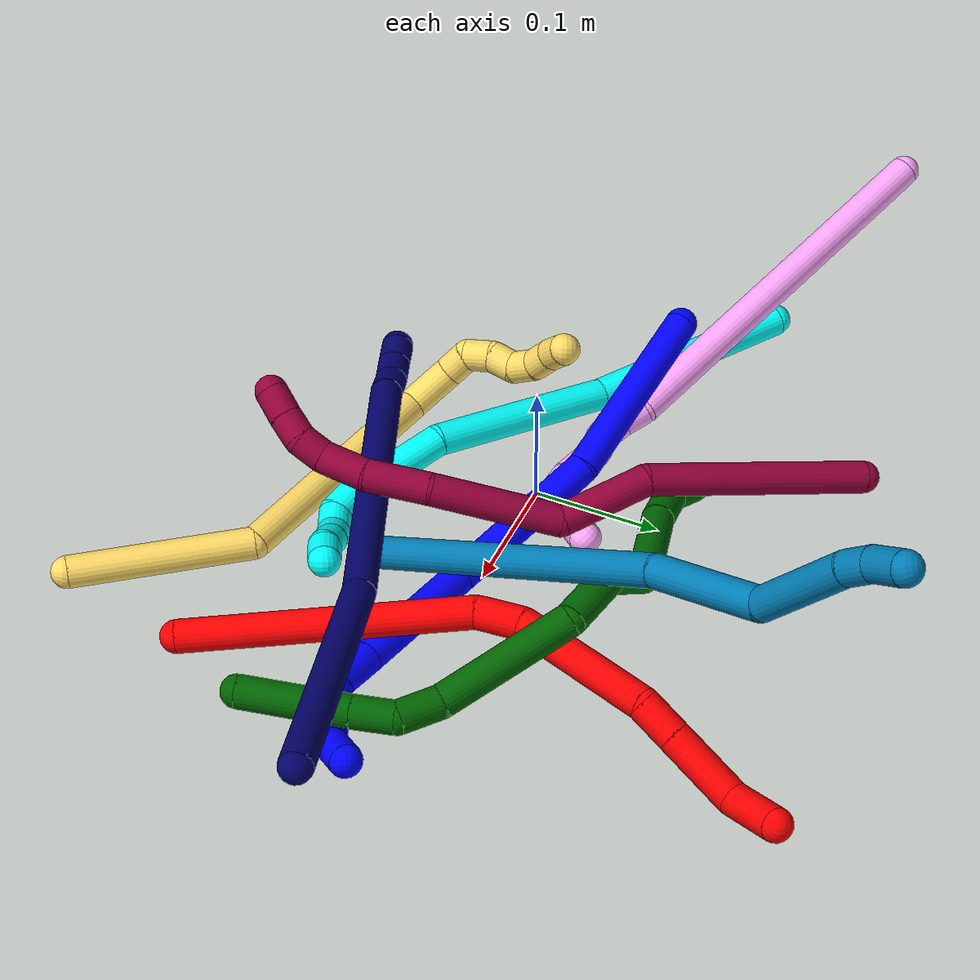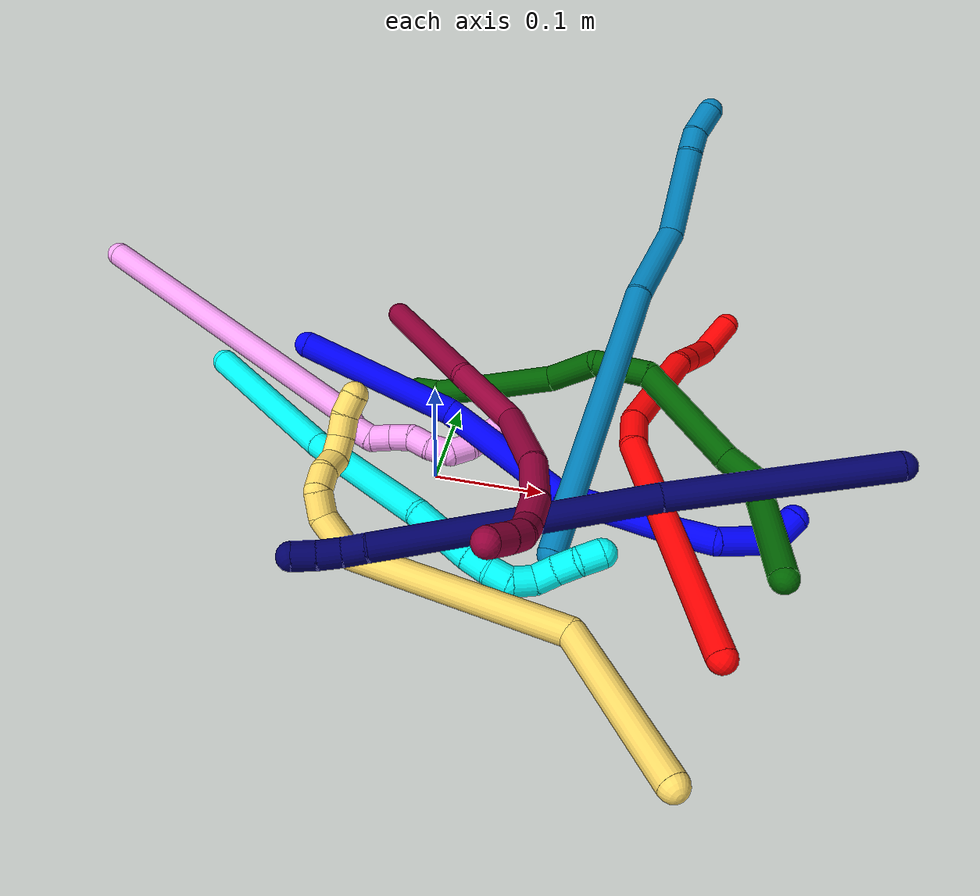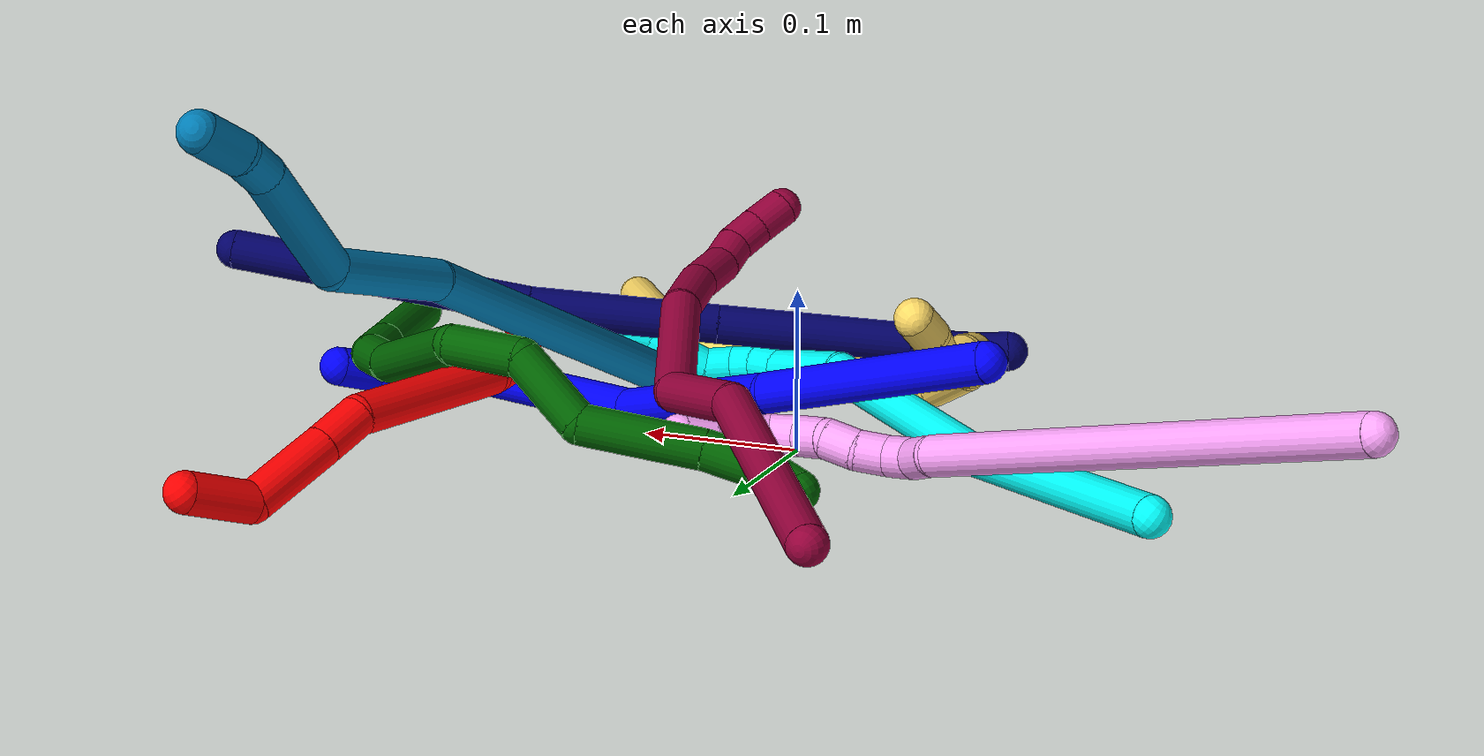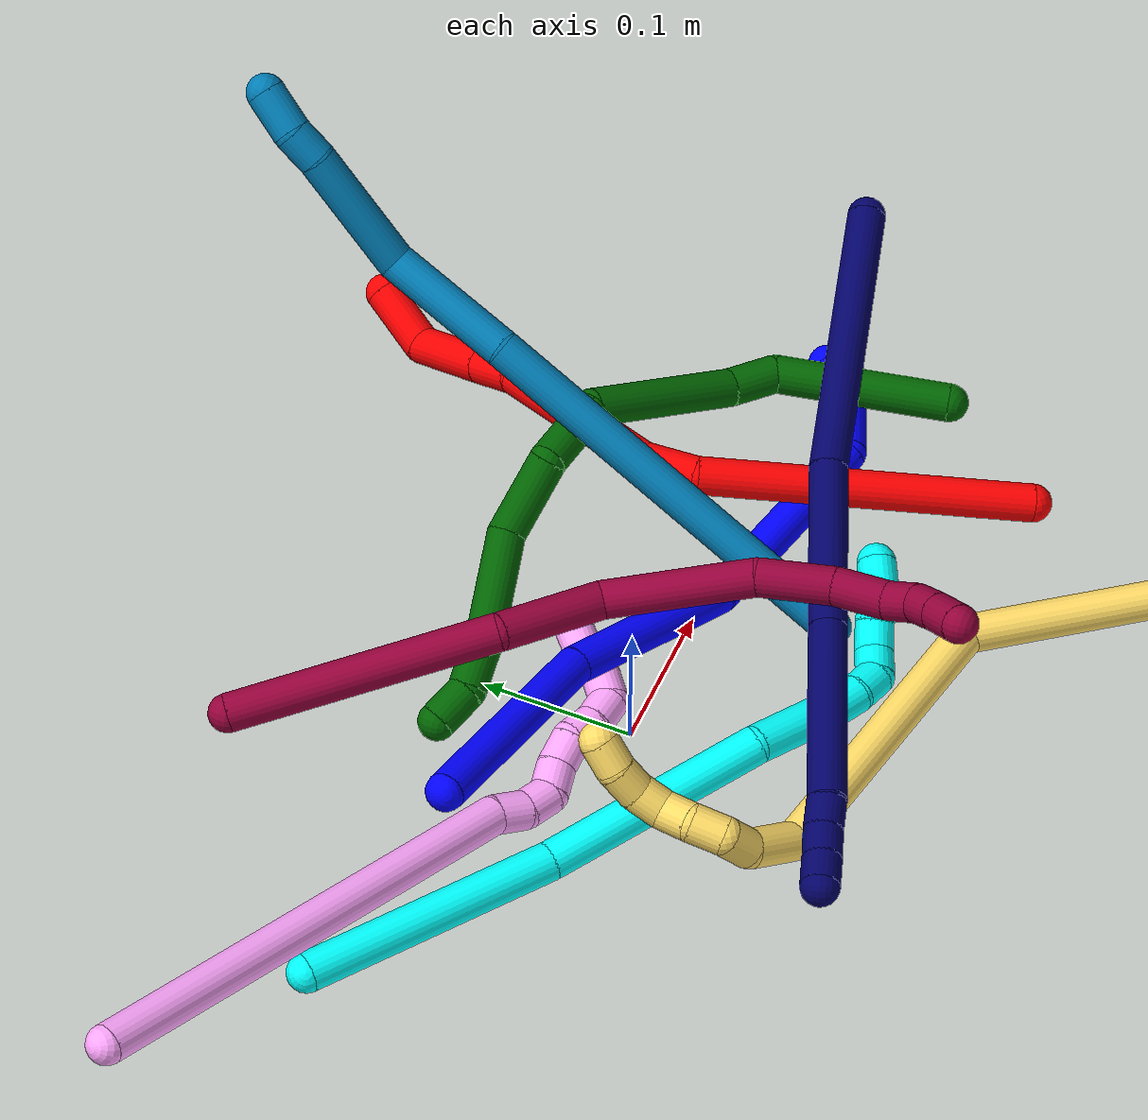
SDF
<sdf version="1.7">
 <world name="default">
  <plugin name="TubeGeneratorPlugin" filename="libtube_generator_plugin.so"/>
  <model name="photoneo_s_sensor">
   <static>1</static>
   <pose>0 0 2 1.57079 1.57079 3.14159</pose>
   <link name="link">
    <inertial><mass>0.1</mass></inertial>
    <sensor name="sensor" type="depth">
     <update_rate>30</update_rate>
     <camera>
      <horizontal_fov>1.22</horizontal_fov>
      <image><width>1920</width><height>1200</height><format>B8G8R8</format></image>
      <clip><near>0.1</near><far>4</far></clip>
      <depth_camera><output>points</output></depth_camera>
     </camera>
     <plugin name="camera_plugin" filename="libgazebo_ros_depth_camera.so">
      <baseline>0.2</baseline>
      <alwaysOn>1</alwaysOn>
      <updateRate>0.0</updateRate>
      <cameraName>camera_ir</cameraName>
      <imageTopicName>/camera/color/image_raw</imageTopicName>
      <cameraInfoTopicName>/camera/color/camera_info</cameraInfoTopicName>
      <depthImageTopicName>/camera/depth/image_raw</depthImageTopicName>
      <depthImageCameraInfoTopicName>/camera/depth/camera_info</depthImageCameraInfoTopicName>
      <pointCloudTopicName>/camera/depth/points</pointCloudTopicName>
      <frameName>fr_optical</frameName>
      <pointCloudCutoff>0.1</pointCloudCutoff>
      <pointCloudCutoffMax>2.0</pointCloudCutoffMax>
      <distortionK1>0</distortionK1>
      <distortionK2>0</distortionK2>
      <distortionK3>0</distortionK3>
      <distortionT1>0</distortionT1>
      <distortionT2>0</distortionT2>
      <CxPrime>0</CxPrime>
      <Cx>0</Cx>
      <Cy>0</Cy>
      <focalLength>0</focalLength>
      <hackBaseline>0</hackBaseline>
     </plugin>
    </sensor>
   </link>
  </model>
  <gravity>0 0 -9.8</gravity>
  <magnetic_field>6e-06 2.3e-05 -4.2e-05</magnetic_field>
  <atmosphere type="adiabatic"/>
  <physics name="default_physics" default="0" type="ode">
   <max_step_size>0.003</max_step_size>
   <real_time_factor>1</real_time_factor>
   <real_time_update_rate>1000</real_time_update_rate>
   <max_contacts>10000</max_contacts>
   <ode>
    <solver>
     <type>quick</type>
     <iters>100</iters>
     <sor>1.3</sor>
     <use_dynamic_moi_rescaling>0</use_dynamic_moi_rescaling>
    </solver>
    <constraints>
     <contact_max_correcting_vel>0</contact_max_correcting_vel>
     <contact_surface_layer>0.001</contact_surface_layer>
     <cfm>0</cfm>
     <erp>0.2</erp>
    </constraints>
   </ode>
  </physics>
  <scene><ambient>0.4 0.4 0.4 1</ambient><background>0.7 0.7 0.7 1</background><shadows>0</shadows></scene>
  <audio><device>default</device></audio>
  <spherical_coordinates>
   <surface_model>EARTH_WGS84</surface_model>
   <latitude_deg>0</latitude_deg>
   <longitude_deg>0</longitude_deg>
   <elevation>0</elevation>
   <heading_deg>0</heading_deg>
  </spherical_coordinates>
  <model name="bin">
   <static>1</static>
   <link name="bottom">
    <collision name="collision-bottom">
     <pose>0 0 -0.01 0 -0 0</pose>
     <geometry><box><size>0.8 0.6 0.02</size></box></geometry>
     <surface>
      <friction><ode><mu>100</mu><mu2>100</mu2></ode></friction>
      <contact><collide_bitmask>65535</collide_bitmask></contact>
     </surface>
    </collision>
   </link>
   <link name="west_wall">
    <collision name="collision-west_wall">
     <pose>-0.41 0 0.1 0 -0 0</pose>
     <geometry><box><size>0.02 0.6 0.2</size></box></geometry>
     <surface>
      <friction><ode><mu>100</mu><mu2>100</mu2></ode></friction>
      <contact><collide_bitmask>65535</collide_bitmask></contact>
     </surface>
    </collision>
   </link>
   <link name="east_wall">
    <collision name="collision-east_wall">
     <pose>0.41 0 0.1 0 -0 0</pose>
     <geometry><box><size>0.02 0.6 0.2</size></box></geometry>
     <surface>
      <friction><ode><mu>100</mu><mu2>100</mu2></ode></friction>
      <contact><collide_bitmask>65535</collide_bitmask></contact>
     </surface>
    </collision>
   </link>
   <link name="south_wall">
    <collision name="collision-south_wall">
     <pose>0 -0.31 0.1 0 -0 0</pose>
     <geometry><box><size>0.8 0.02 0.2</size></box></geometry>
     <surface>
      <friction><ode><mu>100</mu><mu2>100</mu2></ode></friction>
      <contact><collide_bitmask>65535</collide_bitmask></contact>
     </surface>
    </collision>
   </link>
   <link name="north_wall">
    <collision name="collision-north_wall">
     <pose>0 0.31 0.1 0 -0 0</pose>
     <geometry><box><size>0.8 0.02 0.2</size></box></geometry>
     <surface>
      <friction><ode><mu>100</mu><mu2>100</mu2></ode></friction>
      <contact><collide_bitmask>65535</collide_bitmask></contact>
     </surface>
    </collision>
   </link>
  </model>
  <model name="1">
   <static>0</static>
   <link name="1">
    <collision name="collision-cylinder-e_1_1_4">
     <pose>0.044914 -0.021619 0.056949 0.362815 0.635348 0.120477</pose>
     <geometry><cylinder><radius>0.0125</radius><length>0.151365</length></cylinder></geometry>
     <surface>
      <friction><ode><mu>1.16</mu><mu2>1.16</mu2><slip1>0</slip1><slip2>0</slip2></ode></friction>
      <contact><ode><kp>1e+06</kp><kd>1</kd><max_vel>0</max_vel><min_depth>0.001</min_depth></ode></contact>
     </surface>
    </collision>
    <visual name="visual-cylinder-e_1_1_4">
     <pose>0.044914 -0.021619 0.056949 0.362815 0.635348 0.120477</pose>
     <geometry><cylinder><radius>0.0125</radius><length>0.151365</length></cylinder></geometry>
     <material><ambient>0 0 1 1</ambient></material>
    </visual>
    <collision name="collision-cylinder-e_2_4_5">
     <pose>0.139457 -0.051892 0.153822 0.213468 0.882098 0.101069</pose>
     <geometry><cylinder><radius>0.0125</radius><length>0.12856</length></cylinder></geometry>
     <surface>
      <friction><ode><mu>1.16</mu><mu2>1.16</mu2><slip1>0</slip1><slip2>0</slip2></ode></friction>
      <contact><ode><kp>1e+06</kp><kd>1</kd><max_vel>0</max_vel><min_depth>0.001</min_depth></ode></contact>
     </surface>
    </collision>
    <visual name="visual-cylinder-e_2_4_5">
     <pose>0.139457 -0.051892 0.153822 0.213468 0.882098 0.101069</pose>
     <geometry><cylinder><radius>0.0125</radius><length>0.12856</length></cylinder></geometry>
     <material><ambient>0 0 1 1</ambient></material>
    </visual>
    <collision name="collision-cylinder-e_3_5_6">
     <pose>0.226017 -0.084832 0.222298 0.704849 0.777988 0.299236</pose>
     <geometry><cylinder><radius>0.0125</radius><length>0.105239</length></cylinder></geometry>
     <surface>
      <friction><ode><mu>1.16</mu><mu2>1.16</mu2><slip1>0</slip1><slip2>0</slip2></ode></friction>
      <contact><ode><kp>1e+06</kp><kd>1</kd><max_vel>0</max_vel><min_depth>0.001</min_depth></ode></contact>
     </surface>
    </collision>
    <visual name="visual-cylinder-e_3_5_6">
     <pose>0.226017 -0.084832 0.222298 0.704849 0.777988 0.299236</pose>
     <geometry><cylinder><radius>0.0125</radius><length>0.105239</length></cylinder></geometry>
     <material><ambient>0 0 1 1</ambient></material>
    </visual>
    <collision name="collision-cylinder-e_4_6_7">
     <pose>0.275346 -0.118523 0.26002 0.798015 0.756455 0.331989</pose>
     <geometry><cylinder><radius>0.0125</radius><length>0.036126</length></cylinder></geometry>
     <surface>
      <friction><ode><mu>1.16</mu><mu2>1.16</mu2><slip1>0</slip1><slip2>0</slip2></ode></friction>
      <contact><ode><kp>1e+06</kp><kd>1</kd><max_vel>0</max_vel><min_depth>0.001</min_depth></ode></contact>
     </surface>
    </collision>
    <visual name="visual-cylinder-e_4_6_7">
     <pose>0.275346 -0.118523 0.26002 0.798015 0.756455 0.331989</pose>
     <geometry><cylinder><radius>0.0125</radius><length>0.036126</length></cylinder></geometry>
     <material><ambient>0 0 1 1</ambient></material>
    </visual>
    <collision name="collision-cylinder-e_5_7_8">
     <pose>0.291672 -0.142014 0.289212 0.613081 0.159143 0.050467</pose>
     <geometry><cylinder><radius>0.0125</radius><length>0.049585</length></cylinder></geometry>
     <surface>
      <friction><ode><mu>1.16</mu><mu2>1.16</mu2><slip1>0</slip1><slip2>0</slip2></ode></friction>
      <contact><ode><kp>1e+06</kp><kd>1</kd><max_vel>0</max_vel><min_depth>0.001</min_depth></ode></contact>
     </surface>
    </collision>
    <visual name="visual-cylinder-e_5_7_8">
     <pose>0.291672 -0.142014 0.289212 0.613081 0.159143 0.050467</pose>
     <geometry><cylinder><radius>0.0125</radius><length>0.049585</length></cylinder></geometry>
     <material><ambient>0 0 1 1</ambient></material>
    </visual>
    <collision name="collision-cylinder-e_6_8_2">
     <pose>0.290835 -0.168106 0.315956 1.06038 -0.333419 -0.196634</pose>
     <geometry><cylinder><radius>0.0125</radius><length>0.029124</length></cylinder></geometry>
     <surface>
      <friction><ode><mu>1.16</mu><mu2>1.16</mu2><slip1>0</slip1><slip2>0</slip2></ode></friction>
      <contact><ode><kp>1e+06</kp><kd>1</kd><max_vel>0</max_vel><min_depth>0.001</min_depth></ode></contact>
     </surface>
    </collision>
    <visual name="visual-cylinder-e_6_8_2">
     <pose>0.290835 -0.168106 0.315956 1.06038 -0.333419 -0.196634</pose>
     <geometry><cylinder><radius>0.0125</radius><length>0.029124</length></cylinder></geometry>
     <material><ambient>0 0 1 1</ambient></material>
    </visual>
    <collision name="collision-sphere-2">
     <pose>0.286069 -0.180112 0.322678 0 -0 0</pose>
     <geometry><sphere><radius>0.0125</radius></sphere></geometry>
     <surface>
      <friction><ode><mu>1.16</mu><mu2>1.16</mu2><slip1>0</slip1><slip2>0</slip2></ode></friction>
      <contact><ode><kp>1e+06</kp><kd>1</kd><max_vel>0</max_vel><min_depth>0.001</min_depth></ode></contact>
     </surface>
    </collision>
    <visual name="visual-sphere-2">
     <pose>0.286069 -0.180112 0.322678 0 -0 0</pose>
     <geometry><sphere><radius>0.0125</radius></sphere></geometry>
     <material><ambient>0 0 1 1</ambient></material>
    </visual>
    <collision name="collision-sphere-4">
     <pose>0.089829 -0.043238 0.113897 0 -0 0</pose>
     <geometry><sphere><radius>0.0125</radius></sphere></geometry>
     <surface>
      <friction><ode><mu>1.16</mu><mu2>1.16</mu2><slip1>0</slip1><slip2>0</slip2></ode></friction>
      <contact><ode><kp>1e+06</kp><kd>1</kd><max_vel>0</max_vel><min_depth>0.001</min_depth></ode></contact>
     </surface>
    </collision>
    <visual name="visual-sphere-4">
     <pose>0.089829 -0.043238 0.113897 0 -0 0</pose>
     <geometry><sphere><radius>0.0125</radius></sphere></geometry>
     <material><ambient>0 0 1 1</ambient></material>
    </visual>
    <collision name="collision-sphere-1">
     <geometry><sphere><radius>0.0125</radius></sphere></geometry>
     <surface>
      <friction><ode><mu>1.16</mu><mu2>1.16</mu2><slip1>0</slip1><slip2>0</slip2></ode></friction>
      <contact><ode><kp>1e+06</kp><kd>1</kd><max_vel>0</max_vel><min_depth>0.001</min_depth></ode></contact>
     </surface>
    </collision>
    <visual name="visual-sphere-1">
     <geometry><sphere><radius>0.0125</radius></sphere></geometry>
     <material><ambient>0 0 1 1</ambient></material>
    </visual>
    <collision name="collision-sphere-8">
     <pose>0.295601 -0.156099 0.309233 0 -0 0</pose>
     <geometry><sphere><radius>0.0125</radius></sphere></geometry>
     <surface>
      <friction><ode><mu>1.16</mu><mu2>1.16</mu2><slip1>0</slip1><slip2>0</slip2></ode></friction>
      <contact><ode><kp>1e+06</kp><kd>1</kd><max_vel>0</max_vel><min_depth>0.001</min_depth></ode></contact>
     </surface>
    </collision>
    <visual name="visual-sphere-8">
     <pose>0.295601 -0.156099 0.309233 0 -0 0</pose>
     <geometry><sphere><radius>0.0125</radius></sphere></geometry>
     <material><ambient>0 0 1 1</ambient></material>
    </visual>
    <collision name="collision-sphere-5">
     <pose>0.189086 -0.060547 0.193747 0 -0 0</pose>
     <geometry><sphere><radius>0.0125</radius></sphere></geometry>
     <surface>
      <friction><ode><mu>1.16</mu><mu2>1.16</mu2><slip1>0</slip1><slip2>0</slip2></ode></friction>
      <contact><ode><kp>1e+06</kp><kd>1</kd><max_vel>0</max_vel><min_depth>0.001</min_depth></ode></contact>
     </surface>
    </collision>
    <visual name="visual-sphere-5">
     <pose>0.189086 -0.060547 0.193747 0 -0 0</pose>
     <geometry><sphere><radius>0.0125</radius></sphere></geometry>
     <material><ambient>0 0 1 1</ambient></material>
    </visual>
    <collision name="collision-sphere-6">
     <pose>0.262948 -0.109118 0.250848 0 -0 0</pose>
     <geometry><sphere><radius>0.0125</radius></sphere></geometry>
     <surface>
      <friction><ode><mu>1.16</mu><mu2>1.16</mu2><slip1>0</slip1><slip2>0</slip2></ode></friction>
      <contact><ode><kp>1e+06</kp><kd>1</kd><max_vel>0</max_vel><min_depth>0.001</min_depth></ode></contact>
     </surface>
    </collision>
    <visual name="visual-sphere-6">
     <pose>0.262948 -0.109118 0.250848 0 -0 0</pose>
     <geometry><sphere><radius>0.0125</radius></sphere></geometry>
     <material><ambient>0 0 1 1</ambient></material>
    </visual>
    <collision name="collision-sphere-7">
     <pose>0.287743 -0.127929 0.269191 0 -0 0</pose>
     <geometry><sphere><radius>0.0125</radius></sphere></geometry>
     <surface>
      <friction><ode><mu>1.16</mu><mu2>1.16</mu2><slip1>0</slip1><slip2>0</slip2></ode></friction>
      <contact><ode><kp>1e+06</kp><kd>1</kd><max_vel>0</max_vel><min_depth>0.001</min_depth></ode></contact>
     </surface>
    </collision>
    <visual name="visual-sphere-7">
     <pose>0.287743 -0.127929 0.269191 0 -0 0</pose>
     <geometry><sphere><radius>0.0125</radius></sphere></geometry>
     <material><ambient>0 0 1 1</ambient></material>
    </visual>
    <inertial>
     <pose>0.162787 -0.070182 0.169452 0 -0 0</pose>
     <mass>0.5</mass>
     <inertia>
      <ixx>0.000523</ixx>
      <ixy>0</ixy>
      <ixz>0</ixz>
      <iyy>0.000613</iyy>
      <iyz>0</iyz>
      <izz>-0.000198</izz>
     </inertia>
    </inertial>
   </link>
   <pose>-0.140435 0.061318 0.085054 -2.30134 -0.055555 -1.03619</pose>
  </model>
  <model name="2">
   <static>0</static>
   <link name="2">
    <collision name="collision-cylinder-e_1_1_4">
     <pose>0.03514 0.098155 0.033192 -1.24471 0.326964 -0.235603</pose>
     <geometry><cylinder><radius>0.0125</radius><length>0.218824</length></cylinder></geometry>
     <surface>
      <friction><ode><mu>1.16</mu><mu2>1.16</mu2><slip1>0</slip1><slip2>0</slip2></ode></friction>
      <contact><ode><kp>1e+06</kp><kd>1</kd><max_vel>0</max_vel><min_depth>0.001</min_depth></ode></contact>
     </surface>
    </collision>
    <visual name="visual-cylinder-e_1_1_4">
     <pose>0.03514 0.098155 0.033192 -1.24471 0.326964 -0.235603</pose>
     <geometry><cylinder><radius>0.0125</radius><length>0.218824</length></cylinder></geometry>
     <material><ambient>1 0 0 1</ambient></material>
    </visual>
    <collision name="collision-cylinder-e_2_4_5">
     <pose>0.080854 0.208806 0.073558 -1.04965 0.633142 -0.374886</pose>
     <geometry><cylinder><radius>0.0125</radius><length>0.035744</length></cylinder></geometry>
     <surface>
      <friction><ode><mu>1.16</mu><mu2>1.16</mu2><slip1>0</slip1><slip2>0</slip2></ode></friction>
      <contact><ode><kp>1e+06</kp><kd>1</kd><max_vel>0</max_vel><min_depth>0.001</min_depth></ode></contact>
     </surface>
    </collision>
    <visual name="visual-cylinder-e_2_4_5">
     <pose>0.080854 0.208806 0.073558 -1.04965 0.633142 -0.374886</pose>
     <geometry><cylinder><radius>0.0125</radius><length>0.035744</length></cylinder></geometry>
     <material><ambient>1 0 0 1</ambient></material>
    </visual>
    <collision name="collision-cylinder-e_3_5_6">
     <pose>0.133537 0.242118 0.110356 -0.612522 0.860598 -0.288257</pose>
     <geometry><cylinder><radius>0.0125</radius><length>0.111069</length></cylinder></geometry>
     <surface>
      <friction><ode><mu>1.16</mu><mu2>1.16</mu2><slip1>0</slip1><slip2>0</slip2></ode></friction>
      <contact><ode><kp>1e+06</kp><kd>1</kd><max_vel>0</max_vel><min_depth>0.001</min_depth></ode></contact>
     </surface>
    </collision>
    <visual name="visual-cylinder-e_3_5_6">
     <pose>0.133537 0.242118 0.110356 -0.612522 0.860598 -0.288257</pose>
     <geometry><cylinder><radius>0.0125</radius><length>0.111069</length></cylinder></geometry>
     <material><ambient>1 0 0 1</ambient></material>
    </visual>
    <collision name="collision-cylinder-e_4_6_7">
     <pose>0.190061 0.267627 0.1431 -0.984217 1.19822 -0.701828</pose>
     <geometry><cylinder><radius>0.0125</radius><length>0.030957</length></cylinder></geometry>
     <surface>
      <friction><ode><mu>1.16</mu><mu2>1.16</mu2><slip1>0</slip1><slip2>0</slip2></ode></friction>
      <contact><ode><kp>1e+06</kp><kd>1</kd><max_vel>0</max_vel><min_depth>0.001</min_depth></ode></contact>
     </surface>
    </collision>
    <visual name="visual-cylinder-e_4_6_7">
     <pose>0.190061 0.267627 0.1431 -0.984217 1.19822 -0.701828</pose>
     <geometry><cylinder><radius>0.0125</radius><length>0.030957</length></cylinder></geometry>
     <material><ambient>1 0 0 1</ambient></material>
    </visual>
    <collision name="collision-cylinder-e_5_7_8">
     <pose>0.231677 0.281067 0.152605 -0.940181 1.19186 -0.663655</pose>
     <geometry><cylinder><radius>0.0125</radius><length>0.058551</length></cylinder></geometry>
     <surface>
      <friction><ode><mu>1.16</mu><mu2>1.16</mu2><slip1>0</slip1><slip2>0</slip2></ode></friction>
      <contact><ode><kp>1e+06</kp><kd>1</kd><max_vel>0</max_vel><min_depth>0.001</min_depth></ode></contact>
     </surface>
    </collision>
    <visual name="visual-cylinder-e_5_7_8">
     <pose>0.231677 0.281067 0.152605 -0.940181 1.19186 -0.663655</pose>
     <geometry><cylinder><radius>0.0125</radius><length>0.058551</length></cylinder></geometry>
     <material><ambient>1 0 0 1</ambient></material>
    </visual>
    <collision name="collision-cylinder-e_6_8_2">
     <pose>0.271146 0.294505 0.177168 -0.252564 0.578901 -0.075584</pose>
     <geometry><cylinder><radius>0.0125</radius><length>0.044855</length></cylinder></geometry>
     <surface>
      <friction><ode><mu>1.16</mu><mu2>1.16</mu2><slip1>0</slip1><slip2>0</slip2></ode></friction>
      <contact><ode><kp>1e+06</kp><kd>1</kd><max_vel>0</max_vel><min_depth>0.001</min_depth></ode></contact>
     </surface>
    </collision>
    <visual name="visual-cylinder-e_6_8_2">
     <pose>0.271146 0.294505 0.177168 -0.252564 0.578901 -0.075584</pose>
     <geometry><cylinder><radius>0.0125</radius><length>0.044855</length></cylinder></geometry>
     <material><ambient>1 0 0 1</ambient></material>
    </visual>
    <collision name="collision-sphere-2">
     <pose>0.283416 0.299197 0.195346 0 -0 0</pose>
     <geometry><sphere><radius>0.0125</radius></sphere></geometry>
     <surface>
      <friction><ode><mu>1.16</mu><mu2>1.16</mu2><slip1>0</slip1><slip2>0</slip2></ode></friction>
      <contact><ode><kp>1e+06</kp><kd>1</kd><max_vel>0</max_vel><min_depth>0.001</min_depth></ode></contact>
     </surface>
    </collision>
    <visual name="visual-sphere-2">
     <pose>0.283416 0.299197 0.195346 0 -0 0</pose>
     <geometry><sphere><radius>0.0125</radius></sphere></geometry>
     <material><ambient>1 0 0 1</ambient></material>
    </visual>
    <collision name="collision-sphere-4">
     <pose>0.07028 0.19631 0.066385 0 -0 0</pose>
     <geometry><sphere><radius>0.0125</radius></sphere></geometry>
     <surface>
      <friction><ode><mu>1.16</mu><mu2>1.16</mu2><slip1>0</slip1><slip2>0</slip2></ode></friction>
      <contact><ode><kp>1e+06</kp><kd>1</kd><max_vel>0</max_vel><min_depth>0.001</min_depth></ode></contact>
     </surface>
    </collision>
    <visual name="visual-sphere-4">
     <pose>0.07028 0.19631 0.066385 0 -0 0</pose>
     <geometry><sphere><radius>0.0125</radius></sphere></geometry>
     <material><ambient>1 0 0 1</ambient></material>
    </visual>
    <collision name="collision-sphere-1">
     <geometry><sphere><radius>0.0125</radius></sphere></geometry>
     <surface>
      <friction><ode><mu>1.16</mu><mu2>1.16</mu2><slip1>0</slip1><slip2>0</slip2></ode></friction>
      <contact><ode><kp>1e+06</kp><kd>1</kd><max_vel>0</max_vel><min_depth>0.001</min_depth></ode></contact>
     </surface>
    </collision>
    <visual name="visual-sphere-1">
     <geometry><sphere><radius>0.0125</radius></sphere></geometry>
     <material><ambient>1 0 0 1</ambient></material>
    </visual>
    <collision name="collision-sphere-8">
     <pose>0.258875 0.289814 0.158991 0 -0 0</pose>
     <geometry><sphere><radius>0.0125</radius></sphere></geometry>
     <surface>
      <friction><ode><mu>1.16</mu><mu2>1.16</mu2><slip1>0</slip1><slip2>0</slip2></ode></friction>
      <contact><ode><kp>1e+06</kp><kd>1</kd><max_vel>0</max_vel><min_depth>0.001</min_depth></ode></contact>
     </surface>
    </collision>
    <visual name="visual-sphere-8">
     <pose>0.258875 0.289814 0.158991 0 -0 0</pose>
     <geometry><sphere><radius>0.0125</radius></sphere></geometry>
     <material><ambient>1 0 0 1</ambient></material>
    </visual>
    <collision name="collision-sphere-5">
     <pose>0.091429 0.221301 0.080731 0 -0 0</pose>
     <geometry><sphere><radius>0.0125</radius></sphere></geometry>
     <surface>
      <friction><ode><mu>1.16</mu><mu2>1.16</mu2><slip1>0</slip1><slip2>0</slip2></ode></friction>
      <contact><ode><kp>1e+06</kp><kd>1</kd><max_vel>0</max_vel><min_depth>0.001</min_depth></ode></contact>
     </surface>
    </collision>
    <visual name="visual-sphere-5">
     <pose>0.091429 0.221301 0.080731 0 -0 0</pose>
     <geometry><sphere><radius>0.0125</radius></sphere></geometry>
     <material><ambient>1 0 0 1</ambient></material>
    </visual>
    <collision name="collision-sphere-6">
     <pose>0.175645 0.262935 0.139981 0 -0 0</pose>
     <geometry><sphere><radius>0.0125</radius></sphere></geometry>
     <surface>
      <friction><ode><mu>1.16</mu><mu2>1.16</mu2><slip1>0</slip1><slip2>0</slip2></ode></friction>
      <contact><ode><kp>1e+06</kp><kd>1</kd><max_vel>0</max_vel><min_depth>0.001</min_depth></ode></contact>
     </surface>
    </collision>
    <visual name="visual-sphere-6">
     <pose>0.175645 0.262935 0.139981 0 -0 0</pose>
     <geometry><sphere><radius>0.0125</radius></sphere></geometry>
     <material><ambient>1 0 0 1</ambient></material>
    </visual>
    <collision name="collision-sphere-7">
     <pose>0.204478 0.27232 0.146219 0 -0 0</pose>
     <geometry><sphere><radius>0.0125</radius></sphere></geometry>
     <surface>
      <friction><ode><mu>1.16</mu><mu2>1.16</mu2><slip1>0</slip1><slip2>0</slip2></ode></friction>
      <contact><ode><kp>1e+06</kp><kd>1</kd><max_vel>0</max_vel><min_depth>0.001</min_depth></ode></contact>
     </surface>
    </collision>
    <visual name="visual-sphere-7">
     <pose>0.204478 0.27232 0.146219 0 -0 0</pose>
     <geometry><sphere><radius>0.0125</radius></sphere></geometry>
     <material><ambient>1 0 0 1</ambient></material>
    </visual>
    <inertial>
     <pose>0.114044 0.187572 0.086923 0 -0 0</pose>
     <mass>0.5</mass>
     <inertia>
      <ixx>0.000702</ixx>
      <ixy>0</ixy>
      <ixz>0</ixz>
      <iyy>0.000278</iyy>
      <iyz>0</iyz>
      <izz>-0.001235</izz>
     </inertia>
    </inertial>
   </link>
   <pose>0.261569 -0.169474 0.018252 0.129075 0.666361 0.949144</pose>
  </model>
  <model name="3">
   <static>0</static>
   <link name="3">
    <collision name="collision-cylinder-e_1_1_4">
     <pose>0.078138 0.016786 0.027687 -0.545019 1.17796 -0.369155</pose>
     <geometry><cylinder><radius>0.0125</radius><length>0.169162</length></cylinder></geometry>
     <surface>
      <friction><ode><mu>1.16</mu><mu2>1.16</mu2><slip1>0</slip1><slip2>0</slip2></ode></friction>
      <contact><ode><kp>1e+06</kp><kd>1</kd><max_vel>0</max_vel><min_depth>0.001</min_depth></ode></contact>
     </surface>
    </collision>
    <visual name="visual-cylinder-e_1_1_4">
     <pose>0.078138 0.016786 0.027687 -0.545019 1.17796 -0.369155</pose>
     <geometry><cylinder><radius>0.0125</radius><length>0.169162</length></cylinder></geometry>
     <material><ambient>0.003922 1 0.996078 1</ambient></material>
    </visual>
    <collision name="collision-cylinder-e_2_4_5">
     <pose>0.228738 0.042405 0.070101 -0.54027 1.33811 -0.4311</pose>
     <geometry><cylinder><radius>0.0125</radius><length>0.148937</length></cylinder></geometry>
     <surface>
      <friction><ode><mu>1.16</mu><mu2>1.16</mu2><slip1>0</slip1><slip2>0</slip2></ode></friction>
      <contact><ode><kp>1e+06</kp><kd>1</kd><max_vel>0</max_vel><min_depth>0.001</min_depth></ode></contact>
     </surface>
    </collision>
    <visual name="visual-cylinder-e_2_4_5">
     <pose>0.228738 0.042405 0.070101 -0.54027 1.33811 -0.4311</pose>
     <geometry><cylinder><radius>0.0125</radius><length>0.148937</length></cylinder></geometry>
     <material><ambient>0.003922 1 0.996078 1</ambient></material>
    </visual>
    <collision name="collision-cylinder-e_3_5_6">
     <pose>0.327171 0.056741 0.09943 -0.360376 1.02974 -0.2054</pose>
     <geometry><cylinder><radius>0.0125</radius><length>0.060599</length></cylinder></geometry>
     <surface>
      <friction><ode><mu>1.16</mu><mu2>1.16</mu2><slip1>0</slip1><slip2>0</slip2></ode></friction>
      <contact><ode><kp>1e+06</kp><kd>1</kd><max_vel>0</max_vel><min_depth>0.001</min_depth></ode></contact>
     </surface>
    </collision>
    <visual name="visual-cylinder-e_3_5_6">
     <pose>0.327171 0.056741 0.09943 -0.360376 1.02974 -0.2054</pose>
     <geometry><cylinder><radius>0.0125</radius><length>0.060599</length></cylinder></geometry>
     <material><ambient>0.003922 1 0.996078 1</ambient></material>
    </visual>
    <collision name="collision-cylinder-e_4_6_7">
     <pose>0.362619 0.063084 0.118618 -0.181379 1.11374 -0.113116</pose>
     <geometry><cylinder><radius>0.0125</radius><length>0.021123</length></cylinder></geometry>
     <surface>
      <friction><ode><mu>1.16</mu><mu2>1.16</mu2><slip1>0</slip1><slip2>0</slip2></ode></friction>
      <contact><ode><kp>1e+06</kp><kd>1</kd><max_vel>0</max_vel><min_depth>0.001</min_depth></ode></contact>
     </surface>
    </collision>
    <visual name="visual-cylinder-e_4_6_7">
     <pose>0.362619 0.063084 0.118618 -0.181379 1.11374 -0.113116</pose>
     <geometry><cylinder><radius>0.0125</radius><length>0.021123</length></cylinder></geometry>
     <material><ambient>0.003922 1 0.996078 1</ambient></material>
    </visual>
    <collision name="collision-cylinder-e_5_7_8">
     <pose>0.380022 0.063567 0.129326 0.058363 0.912149 0.028637</pose>
     <geometry><cylinder><radius>0.0125</radius><length>0.020044</length></cylinder></geometry>
     <surface>
      <friction><ode><mu>1.16</mu><mu2>1.16</mu2><slip1>0</slip1><slip2>0</slip2></ode></friction>
      <contact><ode><kp>1e+06</kp><kd>1</kd><max_vel>0</max_vel><min_depth>0.001</min_depth></ode></contact>
     </surface>
    </collision>
    <visual name="visual-cylinder-e_5_7_8">
     <pose>0.380022 0.063567 0.129326 0.058363 0.912149 0.028637</pose>
     <geometry><cylinder><radius>0.0125</radius><length>0.020044</length></cylinder></geometry>
     <material><ambient>0.003922 1 0.996078 1</ambient></material>
    </visual>
    <collision name="collision-cylinder-e_6_8_9">
     <pose>0.392555 0.057231 0.1421 0.732207 0.475701 0.185364</pose>
     <geometry><cylinder><radius>0.0125</radius><length>0.02012</length></cylinder></geometry>
     <surface>
      <friction><ode><mu>1.16</mu><mu2>1.16</mu2><slip1>0</slip1><slip2>0</slip2></ode></friction>
      <contact><ode><kp>1e+06</kp><kd>1</kd><max_vel>0</max_vel><min_depth>0.001</min_depth></ode></contact>
     </surface>
    </collision>
    <visual name="visual-cylinder-e_6_8_9">
     <pose>0.392555 0.057231 0.1421 0.732207 0.475701 0.185364</pose>
     <geometry><cylinder><radius>0.0125</radius><length>0.02012</length></cylinder></geometry>
     <material><ambient>0.003922 1 0.996078 1</ambient></material>
    </visual>
    <collision name="collision-cylinder-e_7_9_10">
     <pose>0.403162 0.043458 0.150569 1.34164 0.643261 0.517017</pose>
     <geometry><cylinder><radius>0.0125</radius><length>0.020005</length></cylinder></geometry>
     <surface>
      <friction><ode><mu>1.16</mu><mu2>1.16</mu2><slip1>0</slip1><slip2>0</slip2></ode></friction>
      <contact><ode><kp>1e+06</kp><kd>1</kd><max_vel>0</max_vel><min_depth>0.001</min_depth></ode></contact>
     </surface>
    </collision>
    <visual name="visual-cylinder-e_7_9_10">
     <pose>0.403162 0.043458 0.150569 1.34164 0.643261 0.517017</pose>
     <geometry><cylinder><radius>0.0125</radius><length>0.020005</length></cylinder></geometry>
     <material><ambient>0.003922 1 0.996078 1</ambient></material>
    </visual>
    <collision name="collision-cylinder-e_8_10_11">
     <pose>0.416244 0.028691 0.153518 1.41002 0.786703 0.678866</pose>
     <geometry><cylinder><radius>0.0125</radius><length>0.020005</length></cylinder></geometry>
     <surface>
      <friction><ode><mu>1.16</mu><mu2>1.16</mu2><slip1>0</slip1><slip2>0</slip2></ode></friction>
      <contact><ode><kp>1e+06</kp><kd>1</kd><max_vel>0</max_vel><min_depth>0.001</min_depth></ode></contact>
     </surface>
    </collision>
    <visual name="visual-cylinder-e_8_10_11">
     <pose>0.416244 0.028691 0.153518 1.41002 0.786703 0.678866</pose>
     <geometry><cylinder><radius>0.0125</radius><length>0.020005</length></cylinder></geometry>
     <material><ambient>0.003922 1 0.996078 1</ambient></material>
    </visual>
    <collision name="collision-cylinder-e_9_11_2">
     <pose>0.4281 0.014028 0.158905 1.06528 0.497603 0.297317</pose>
     <geometry><cylinder><radius>0.0125</radius><length>0.020006</length></cylinder></geometry>
     <surface>
      <friction><ode><mu>1.16</mu><mu2>1.16</mu2><slip1>0</slip1><slip2>0</slip2></ode></friction>
      <contact><ode><kp>1e+06</kp><kd>1</kd><max_vel>0</max_vel><min_depth>0.001</min_depth></ode></contact>
     </surface>
    </collision>
    <visual name="visual-cylinder-e_9_11_2">
     <pose>0.4281 0.014028 0.158905 1.06528 0.497603 0.297317</pose>
     <geometry><cylinder><radius>0.0125</radius><length>0.020006</length></cylinder></geometry>
     <material><ambient>0.003922 1 0.996078 1</ambient></material>
    </visual>
    <collision name="collision-sphere-2">
     <pose>0.432875 0.006338 0.163162 0 -0 0</pose>
     <geometry><sphere><radius>0.0125</radius></sphere></geometry>
     <surface>
      <friction><ode><mu>1.16</mu><mu2>1.16</mu2><slip1>0</slip1><slip2>0</slip2></ode></friction>
      <contact><ode><kp>1e+06</kp><kd>1</kd><max_vel>0</max_vel><min_depth>0.001</min_depth></ode></contact>
     </surface>
    </collision>
    <visual name="visual-sphere-2">
     <pose>0.432875 0.006338 0.163162 0 -0 0</pose>
     <geometry><sphere><radius>0.0125</radius></sphere></geometry>
     <material><ambient>0.003922 1 0.996078 1</ambient></material>
    </visual>
    <collision name="collision-sphere-11">
     <pose>0.423326 0.021719 0.154649 0 -0 0</pose>
     <geometry><sphere><radius>0.0125</radius></sphere></geometry>
     <surface>
      <friction><ode><mu>1.16</mu><mu2>1.16</mu2><slip1>0</slip1><slip2>0</slip2></ode></friction>
      <contact><ode><kp>1e+06</kp><kd>1</kd><max_vel>0</max_vel><min_depth>0.001</min_depth></ode></contact>
     </surface>
    </collision>
    <visual name="visual-sphere-11">
     <pose>0.423326 0.021719 0.154649 0 -0 0</pose>
     <geometry><sphere><radius>0.0125</radius></sphere></geometry>
     <material><ambient>0.003922 1 0.996078 1</ambient></material>
    </visual>
    <collision name="collision-sphere-10">
     <pose>0.409161 0.035664 0.152387 0 -0 0</pose>
     <geometry><sphere><radius>0.0125</radius></sphere></geometry>
     <surface>
      <friction><ode><mu>1.16</mu><mu2>1.16</mu2><slip1>0</slip1><slip2>0</slip2></ode></friction>
      <contact><ode><kp>1e+06</kp><kd>1</kd><max_vel>0</max_vel><min_depth>0.001</min_depth></ode></contact>
     </surface>
    </collision>
    <visual name="visual-sphere-10">
     <pose>0.409161 0.035664 0.152387 0 -0 0</pose>
     <geometry><sphere><radius>0.0125</radius></sphere></geometry>
     <material><ambient>0.003922 1 0.996078 1</ambient></material>
    </visual>
    <collision name="collision-sphere-9">
     <pose>0.397162 0.051252 0.148751 0 -0 0</pose>
     <geometry><sphere><radius>0.0125</radius></sphere></geometry>
     <surface>
      <friction><ode><mu>1.16</mu><mu2>1.16</mu2><slip1>0</slip1><slip2>0</slip2></ode></friction>
      <contact><ode><kp>1e+06</kp><kd>1</kd><max_vel>0</max_vel><min_depth>0.001</min_depth></ode></contact>
     </surface>
    </collision>
    <visual name="visual-sphere-9">
     <pose>0.397162 0.051252 0.148751 0 -0 0</pose>
     <geometry><sphere><radius>0.0125</radius></sphere></geometry>
     <material><ambient>0.003922 1 0.996078 1</ambient></material>
    </visual>
    <collision name="collision-sphere-4">
     <pose>0.156276 0.033572 0.055375 0 -0 0</pose>
     <geometry><sphere><radius>0.0125</radius></sphere></geometry>
     <surface>
      <friction><ode><mu>1.16</mu><mu2>1.16</mu2><slip1>0</slip1><slip2>0</slip2></ode></friction>
      <contact><ode><kp>1e+06</kp><kd>1</kd><max_vel>0</max_vel><min_depth>0.001</min_depth></ode></contact>
     </surface>
    </collision>
    <visual name="visual-sphere-4">
     <pose>0.156276 0.033572 0.055375 0 -0 0</pose>
     <geometry><sphere><radius>0.0125</radius></sphere></geometry>
     <material><ambient>0.003922 1 0.996078 1</ambient></material>
    </visual>
    <collision name="collision-sphere-1">
     <geometry><sphere><radius>0.0125</radius></sphere></geometry>
     <surface>
      <friction><ode><mu>1.16</mu><mu2>1.16</mu2><slip1>0</slip1><slip2>0</slip2></ode></friction>
      <contact><ode><kp>1e+06</kp><kd>1</kd><max_vel>0</max_vel><min_depth>0.001</min_depth></ode></contact>
     </surface>
    </collision>
    <visual name="visual-sphere-1">
     <geometry><sphere><radius>0.0125</radius></sphere></geometry>
     <material><ambient>0.003922 1 0.996078 1</ambient></material>
    </visual>
    <collision name="collision-sphere-8">
     <pose>0.387948 0.063209 0.135449 0 -0 0</pose>
     <geometry><sphere><radius>0.0125</radius></sphere></geometry>
     <surface>
      <friction><ode><mu>1.16</mu><mu2>1.16</mu2><slip1>0</slip1><slip2>0</slip2></ode></friction>
      <contact><ode><kp>1e+06</kp><kd>1</kd><max_vel>0</max_vel><min_depth>0.001</min_depth></ode></contact>
     </surface>
    </collision>
    <visual name="visual-sphere-8">
     <pose>0.387948 0.063209 0.135449 0 -0 0</pose>
     <geometry><sphere><radius>0.0125</radius></sphere></geometry>
     <material><ambient>0.003922 1 0.996078 1</ambient></material>
    </visual>
    <collision name="collision-sphere-5">
     <pose>0.301199 0.051238 0.084827 0 -0 0</pose>
     <geometry><sphere><radius>0.0125</radius></sphere></geometry>
     <surface>
      <friction><ode><mu>1.16</mu><mu2>1.16</mu2><slip1>0</slip1><slip2>0</slip2></ode></friction>
      <contact><ode><kp>1e+06</kp><kd>1</kd><max_vel>0</max_vel><min_depth>0.001</min_depth></ode></contact>
     </surface>
    </collision>
    <visual name="visual-sphere-5">
     <pose>0.301199 0.051238 0.084827 0 -0 0</pose>
     <geometry><sphere><radius>0.0125</radius></sphere></geometry>
     <material><ambient>0.003922 1 0.996078 1</ambient></material>
    </visual>
    <collision name="collision-sphere-6">
     <pose>0.353142 0.062244 0.114033 0 -0 0</pose>
     <geometry><sphere><radius>0.0125</radius></sphere></geometry>
     <surface>
      <friction><ode><mu>1.16</mu><mu2>1.16</mu2><slip1>0</slip1><slip2>0</slip2></ode></friction>
      <contact><ode><kp>1e+06</kp><kd>1</kd><max_vel>0</max_vel><min_depth>0.001</min_depth></ode></contact>
     </surface>
    </collision>
    <visual name="visual-sphere-6">
     <pose>0.353142 0.062244 0.114033 0 -0 0</pose>
     <geometry><sphere><radius>0.0125</radius></sphere></geometry>
     <material><ambient>0.003922 1 0.996078 1</ambient></material>
    </visual>
    <collision name="collision-sphere-7">
     <pose>0.372097 0.063925 0.123202 0 -0 0</pose>
     <geometry><sphere><radius>0.0125</radius></sphere></geometry>
     <surface>
      <friction><ode><mu>1.16</mu><mu2>1.16</mu2><slip1>0</slip1><slip2>0</slip2></ode></friction>
      <contact><ode><kp>1e+06</kp><kd>1</kd><max_vel>0</max_vel><min_depth>0.001</min_depth></ode></contact>
     </surface>
    </collision>
    <visual name="visual-sphere-7">
     <pose>0.372097 0.063925 0.123202 0 -0 0</pose>
     <geometry><sphere><radius>0.0125</radius></sphere></geometry>
     <material><ambient>0.003922 1 0.996078 1</ambient></material>
    </visual>
    <inertial>
     <pose>0.230486 0.036152 0.076737 0 -0 0</pose>
     <mass>0.5</mass>
     <inertia>
      <ixx>0.000171</ixx>
      <ixy>0</ixy>
      <ixz>0</ixz>
      <iyy>0.000619</iyy>
      <iyz>0</iyz>
      <izz>-0.000778</izz>
     </inertia>
    </inertial>
   </link>
   <pose>-0.2523 0.103724 0.018536 -2.57384 -0.351112 -0.633515</pose>
  </model>
  <model name="4">
   <static>0</static>
   <link name="4">
    <collision name="collision-cylinder-e_1_1_4">
     <pose>0.04089 -0.027912 -0.150019 2.95764 0.261817 1.91938</pose>
     <geometry><cylinder><radius>0.0125</radius><length>0.315954</length></cylinder></geometry>
     <surface>
      <friction><ode><mu>1.16</mu><mu2>1.16</mu2><slip1>0</slip1><slip2>0</slip2></ode></friction>
      <contact><ode><kp>1e+06</kp><kd>1</kd><max_vel>0</max_vel><min_depth>0.001</min_depth></ode></contact>
     </surface>
    </collision>
    <visual name="visual-cylinder-e_1_1_4">
     <pose>0.04089 -0.027912 -0.150019 2.95764 0.261817 1.91938</pose>
     <geometry><cylinder><radius>0.0125</radius><length>0.315954</length></cylinder></geometry>
     <material><ambient>1 0.65098 0.996078 1</ambient></material>
    </visual>
    <collision name="collision-cylinder-e_2_4_5">
     <pose>0.081058 -0.058511 -0.31083 2.89765 -0.064869 -0.517516</pose>
     <geometry><cylinder><radius>0.0125</radius><length>0.022291</length></cylinder></geometry>
     <surface>
      <friction><ode><mu>1.16</mu><mu2>1.16</mu2><slip1>0</slip1><slip2>0</slip2></ode></friction>
      <contact><ode><kp>1e+06</kp><kd>1</kd><max_vel>0</max_vel><min_depth>0.001</min_depth></ode></contact>
     </surface>
    </collision>
    <visual name="visual-cylinder-e_2_4_5">
     <pose>0.081058 -0.058511 -0.31083 2.89765 -0.064869 -0.517516</pose>
     <geometry><cylinder><radius>0.0125</radius><length>0.022291</length></cylinder></geometry>
     <material><ambient>1 0.65098 0.996078 1</ambient></material>
    </visual>
    <collision name="collision-cylinder-e_3_5_6">
     <pose>0.083205 -0.063934 -0.330883 2.85421 0.288888 1.5761</pose>
     <geometry><cylinder><radius>0.0125</radius><length>0.020148</length></cylinder></geometry>
     <surface>
      <friction><ode><mu>1.16</mu><mu2>1.16</mu2><slip1>0</slip1><slip2>0</slip2></ode></friction>
      <contact><ode><kp>1e+06</kp><kd>1</kd><max_vel>0</max_vel><min_depth>0.001</min_depth></ode></contact>
     </surface>
    </collision>
    <visual name="visual-cylinder-e_3_5_6">
     <pose>0.083205 -0.063934 -0.330883 2.85421 0.288888 1.5761</pose>
     <geometry><cylinder><radius>0.0125</radius><length>0.020148</length></cylinder></geometry>
     <material><ambient>1 0.65098 0.996078 1</ambient></material>
    </visual>
    <collision name="collision-cylinder-e_4_6_7">
     <pose>0.094138 -0.068069 -0.346057 2.90952 0.925022 2.68228</pose>
     <geometry><cylinder><radius>0.0125</radius><length>0.020192</length></cylinder></geometry>
     <surface>
      <friction><ode><mu>1.16</mu><mu2>1.16</mu2><slip1>0</slip1><slip2>0</slip2></ode></friction>
      <contact><ode><kp>1e+06</kp><kd>1</kd><max_vel>0</max_vel><min_depth>0.001</min_depth></ode></contact>
     </surface>
    </collision>
    <visual name="visual-cylinder-e_4_6_7">
     <pose>0.094138 -0.068069 -0.346057 2.90952 0.925022 2.68228</pose>
     <geometry><cylinder><radius>0.0125</radius><length>0.020192</length></cylinder></geometry>
     <material><ambient>1 0.65098 0.996078 1</ambient></material>
    </visual>
    <collision name="collision-cylinder-e_5_7_8">
     <pose>0.109158 -0.073196 -0.358509 2.62317 0.745979 1.95043</pose>
     <geometry><cylinder><radius>0.0125</radius><length>0.020501</length></cylinder></geometry>
     <surface>
      <friction><ode><mu>1.16</mu><mu2>1.16</mu2><slip1>0</slip1><slip2>0</slip2></ode></friction>
      <contact><ode><kp>1e+06</kp><kd>1</kd><max_vel>0</max_vel><min_depth>0.001</min_depth></ode></contact>
     </surface>
    </collision>
    <visual name="visual-cylinder-e_5_7_8">
     <pose>0.109158 -0.073196 -0.358509 2.62317 0.745979 1.95043</pose>
     <geometry><cylinder><radius>0.0125</radius><length>0.020501</length></cylinder></geometry>
     <material><ambient>1 0.65098 0.996078 1</ambient></material>
    </visual>
    <collision name="collision-cylinder-e_6_8_9">
     <pose>0.119517 -0.079565 -0.374135 2.85905 0.345117 1.77278</pose>
     <geometry><cylinder><radius>0.0125</radius><length>0.02011</length></cylinder></geometry>
     <surface>
      <friction><ode><mu>1.16</mu><mu2>1.16</mu2><slip1>0</slip1><slip2>0</slip2></ode></friction>
      <contact><ode><kp>1e+06</kp><kd>1</kd><max_vel>0</max_vel><min_depth>0.001</min_depth></ode></contact>
     </surface>
    </collision>
    <visual name="visual-cylinder-e_6_8_9">
     <pose>0.119517 -0.079565 -0.374135 2.85905 0.345117 1.77278</pose>
     <geometry><cylinder><radius>0.0125</radius><length>0.02011</length></cylinder></geometry>
     <material><ambient>1 0.65098 0.996078 1</ambient></material>
    </visual>
    <collision name="collision-cylinder-e_7_9_10">
     <pose>0.128647 -0.083652 -0.391626 2.97085 0.59153 2.59399</pose>
     <geometry><cylinder><radius>0.0125</radius><length>0.020546</length></cylinder></geometry>
     <surface>
      <friction><ode><mu>1.16</mu><mu2>1.16</mu2><slip1>0</slip1><slip2>0</slip2></ode></friction>
      <contact><ode><kp>1e+06</kp><kd>1</kd><max_vel>0</max_vel><min_depth>0.001</min_depth></ode></contact>
     </surface>
    </collision>
    <visual name="visual-cylinder-e_7_9_10">
     <pose>0.128647 -0.083652 -0.391626 2.97085 0.59153 2.59399</pose>
     <geometry><cylinder><radius>0.0125</radius><length>0.020546</length></cylinder></geometry>
     <material><ambient>1 0.65098 0.996078 1</ambient></material>
    </visual>
    <collision name="collision-cylinder-e_8_10_11">
     <pose>0.143649 -0.08264 -0.403111 -2.4678 1.16873 -2.16759</pose>
     <geometry><cylinder><radius>0.0125</radius><length>0.020155</length></cylinder></geometry>
     <surface>
      <friction><ode><mu>1.16</mu><mu2>1.16</mu2><slip1>0</slip1><slip2>0</slip2></ode></friction>
      <contact><ode><kp>1e+06</kp><kd>1</kd><max_vel>0</max_vel><min_depth>0.001</min_depth></ode></contact>
     </surface>
    </collision>
    <visual name="visual-cylinder-e_8_10_11">
     <pose>0.143649 -0.08264 -0.403111 -2.4678 1.16873 -2.16759</pose>
     <geometry><cylinder><radius>0.0125</radius><length>0.020155</length></cylinder></geometry>
     <material><ambient>1 0.65098 0.996078 1</ambient></material>
    </visual>
    <collision name="collision-cylinder-e_9_11_12">
     <pose>0.162402 -0.076944 -0.406139 -1.55433 1.24179 -1.22625</pose>
     <geometry><cylinder><radius>0.0125</radius><length>0.020032</length></cylinder></geometry>
     <surface>
      <friction><ode><mu>1.16</mu><mu2>1.16</mu2><slip1>0</slip1><slip2>0</slip2></ode></friction>
      <contact><ode><kp>1e+06</kp><kd>1</kd><max_vel>0</max_vel><min_depth>0.001</min_depth></ode></contact>
     </surface>
    </collision>
    <visual name="visual-cylinder-e_9_11_12">
     <pose>0.162402 -0.076944 -0.406139 -1.55433 1.24179 -1.22625</pose>
     <geometry><cylinder><radius>0.0125</radius><length>0.020032</length></cylinder></geometry>
     <material><ambient>1 0.65098 0.996078 1</ambient></material>
    </visual>
    <collision name="collision-cylinder-e_10_12_2">
     <pose>0.181766 -0.072253 -0.407021 -2.14192 1.39753 -1.98889</pose>
     <geometry><cylinder><radius>0.0125</radius><length>0.020071</length></cylinder></geometry>
     <surface>
      <friction><ode><mu>1.16</mu><mu2>1.16</mu2><slip1>0</slip1><slip2>0</slip2></ode></friction>
      <contact><ode><kp>1e+06</kp><kd>1</kd><max_vel>0</max_vel><min_depth>0.001</min_depth></ode></contact>
     </surface>
    </collision>
    <visual name="visual-cylinder-e_10_12_2">
     <pose>0.181766 -0.072253 -0.407021 -2.14192 1.39753 -1.98889</pose>
     <geometry><cylinder><radius>0.0125</radius><length>0.020071</length></cylinder></geometry>
     <material><ambient>1 0.65098 0.996078 1</ambient></material>
    </visual>
    <collision name="collision-sphere-2">
     <pose>0.191651 -0.070797 -0.407957 0 -0 0</pose>
     <geometry><sphere><radius>0.0125</radius></sphere></geometry>
     <surface>
      <friction><ode><mu>1.16</mu><mu2>1.16</mu2><slip1>0</slip1><slip2>0</slip2></ode></friction>
      <contact><ode><kp>1e+06</kp><kd>1</kd><max_vel>0</max_vel><min_depth>0.001</min_depth></ode></contact>
     </surface>
    </collision>
    <visual name="visual-sphere-2">
     <pose>0.191651 -0.070797 -0.407957 0 -0 0</pose>
     <geometry><sphere><radius>0.0125</radius></sphere></geometry>
     <material><ambient>1 0.65098 0.996078 1</ambient></material>
    </visual>
    <collision name="collision-sphere-12">
     <pose>0.17188 -0.073708 -0.406086 0 -0 0</pose>
     <geometry><sphere><radius>0.0125</radius></sphere></geometry>
     <surface>
      <friction><ode><mu>1.16</mu><mu2>1.16</mu2><slip1>0</slip1><slip2>0</slip2></ode></friction>
      <contact><ode><kp>1e+06</kp><kd>1</kd><max_vel>0</max_vel><min_depth>0.001</min_depth></ode></contact>
     </surface>
    </collision>
    <visual name="visual-sphere-12">
     <pose>0.17188 -0.073708 -0.406086 0 -0 0</pose>
     <geometry><sphere><radius>0.0125</radius></sphere></geometry>
     <material><ambient>1 0.65098 0.996078 1</ambient></material>
    </visual>
    <collision name="collision-sphere-11">
     <pose>0.152923 -0.08018 -0.406193 0 -0 0</pose>
     <geometry><sphere><radius>0.0125</radius></sphere></geometry>
     <surface>
      <friction><ode><mu>1.16</mu><mu2>1.16</mu2><slip1>0</slip1><slip2>0</slip2></ode></friction>
      <contact><ode><kp>1e+06</kp><kd>1</kd><max_vel>0</max_vel><min_depth>0.001</min_depth></ode></contact>
     </surface>
    </collision>
    <visual name="visual-sphere-11">
     <pose>0.152923 -0.08018 -0.406193 0 -0 0</pose>
     <geometry><sphere><radius>0.0125</radius></sphere></geometry>
     <material><ambient>1 0.65098 0.996078 1</ambient></material>
    </visual>
    <collision name="collision-sphere-10">
     <pose>0.134376 -0.085101 -0.40003 0 -0 0</pose>
     <geometry><sphere><radius>0.0125</radius></sphere></geometry>
     <surface>
      <friction><ode><mu>1.16</mu><mu2>1.16</mu2><slip1>0</slip1><slip2>0</slip2></ode></friction>
      <contact><ode><kp>1e+06</kp><kd>1</kd><max_vel>0</max_vel><min_depth>0.001</min_depth></ode></contact>
     </surface>
    </collision>
    <visual name="visual-sphere-10">
     <pose>0.134376 -0.085101 -0.40003 0 -0 0</pose>
     <geometry><sphere><radius>0.0125</radius></sphere></geometry>
     <material><ambient>1 0.65098 0.996078 1</ambient></material>
    </visual>
    <collision name="collision-sphere-9">
     <pose>0.122918 -0.082203 -0.383222 0 -0 0</pose>
     <geometry><sphere><radius>0.0125</radius></sphere></geometry>
     <surface>
      <friction><ode><mu>1.16</mu><mu2>1.16</mu2><slip1>0</slip1><slip2>0</slip2></ode></friction>
      <contact><ode><kp>1e+06</kp><kd>1</kd><max_vel>0</max_vel><min_depth>0.001</min_depth></ode></contact>
     </surface>
    </collision>
    <visual name="visual-sphere-9">
     <pose>0.122918 -0.082203 -0.383222 0 -0 0</pose>
     <geometry><sphere><radius>0.0125</radius></sphere></geometry>
     <material><ambient>1 0.65098 0.996078 1</ambient></material>
    </visual>
    <collision name="collision-sphere-4">
     <pose>0.08178 -0.055825 -0.300037 0 -0 0</pose>
     <geometry><sphere><radius>0.0125</radius></sphere></geometry>
     <surface>
      <friction><ode><mu>1.16</mu><mu2>1.16</mu2><slip1>0</slip1><slip2>0</slip2></ode></friction>
      <contact><ode><kp>1e+06</kp><kd>1</kd><max_vel>0</max_vel><min_depth>0.001</min_depth></ode></contact>
     </surface>
    </collision>
    <visual name="visual-sphere-4">
     <pose>0.08178 -0.055825 -0.300037 0 -0 0</pose>
     <geometry><sphere><radius>0.0125</radius></sphere></geometry>
     <material><ambient>1 0.65098 0.996078 1</ambient></material>
    </visual>
    <collision name="collision-sphere-1">
     <geometry><sphere><radius>0.0125</radius></sphere></geometry>
     <surface>
      <friction><ode><mu>1.16</mu><mu2>1.16</mu2><slip1>0</slip1><slip2>0</slip2></ode></friction>
      <contact><ode><kp>1e+06</kp><kd>1</kd><max_vel>0</max_vel><min_depth>0.001</min_depth></ode></contact>
     </surface>
    </collision>
    <visual name="visual-sphere-1">
     <geometry><sphere><radius>0.0125</radius></sphere></geometry>
     <material><ambient>1 0.65098 0.996078 1</ambient></material>
    </visual>
    <collision name="collision-sphere-8">
     <pose>0.116115 -0.076927 -0.365048 0 -0 0</pose>
     <geometry><sphere><radius>0.0125</radius></sphere></geometry>
     <surface>
      <friction><ode><mu>1.16</mu><mu2>1.16</mu2><slip1>0</slip1><slip2>0</slip2></ode></friction>
      <contact><ode><kp>1e+06</kp><kd>1</kd><max_vel>0</max_vel><min_depth>0.001</min_depth></ode></contact>
     </surface>
    </collision>
    <visual name="visual-sphere-8">
     <pose>0.116115 -0.076927 -0.365048 0 -0 0</pose>
     <geometry><sphere><radius>0.0125</radius></sphere></geometry>
     <material><ambient>1 0.65098 0.996078 1</ambient></material>
    </visual>
    <collision name="collision-sphere-5">
     <pose>0.080335 -0.061197 -0.321623 0 -0 0</pose>
     <geometry><sphere><radius>0.0125</radius></sphere></geometry>
     <surface>
      <friction><ode><mu>1.16</mu><mu2>1.16</mu2><slip1>0</slip1><slip2>0</slip2></ode></friction>
      <contact><ode><kp>1e+06</kp><kd>1</kd><max_vel>0</max_vel><min_depth>0.001</min_depth></ode></contact>
     </surface>
    </collision>
    <visual name="visual-sphere-5">
     <pose>0.080335 -0.061197 -0.321623 0 -0 0</pose>
     <geometry><sphere><radius>0.0125</radius></sphere></geometry>
     <material><ambient>1 0.65098 0.996078 1</ambient></material>
    </visual>
    <collision name="collision-sphere-6">
     <pose>0.086075 -0.066671 -0.340144 0 -0 0</pose>
     <geometry><sphere><radius>0.0125</radius></sphere></geometry>
     <surface>
      <friction><ode><mu>1.16</mu><mu2>1.16</mu2><slip1>0</slip1><slip2>0</slip2></ode></friction>
      <contact><ode><kp>1e+06</kp><kd>1</kd><max_vel>0</max_vel><min_depth>0.001</min_depth></ode></contact>
     </surface>
    </collision>
    <visual name="visual-sphere-6">
     <pose>0.086075 -0.066671 -0.340144 0 -0 0</pose>
     <geometry><sphere><radius>0.0125</radius></sphere></geometry>
     <material><ambient>1 0.65098 0.996078 1</ambient></material>
    </visual>
    <collision name="collision-sphere-7">
     <pose>0.102201 -0.069466 -0.35197 0 -0 0</pose>
     <geometry><sphere><radius>0.0125</radius></sphere></geometry>
     <surface>
      <friction><ode><mu>1.16</mu><mu2>1.16</mu2><slip1>0</slip1><slip2>0</slip2></ode></friction>
      <contact><ode><kp>1e+06</kp><kd>1</kd><max_vel>0</max_vel><min_depth>0.001</min_depth></ode></contact>
     </surface>
    </collision>
    <visual name="visual-sphere-7">
     <pose>0.102201 -0.069466 -0.35197 0 -0 0</pose>
     <geometry><sphere><radius>0.0125</radius></sphere></geometry>
     <material><ambient>1 0.65098 0.996078 1</ambient></material>
    </visual>
    <inertial>
     <pose>0.07077 -0.044525 -0.230664 0 -0 0</pose>
     <mass>0.5</mass>
     <inertia>
      <ixx>0.001543</ixx>
      <ixy>0</ixy>
      <ixz>0</ixz>
      <iyy>0.003406</iyy>
      <iyz>0</iyz>
      <izz>-0.000256</izz>
     </inertia>
    </inertial>
   </link>
   <pose>-0.388361 0.162406 0.096436 -0.998254 -0.397315 0.784445</pose>
  </model>
  <model name="5">
   <static>0</static>
   <link name="5">
    <collision name="collision-cylinder-e_1_1_4">
     <pose>-0.010032 0.005357 -0.069463 -3.06463 -0.143018 2.15519</pose>
     <geometry><cylinder><radius>0.0125</radius><length>0.140775</length></cylinder></geometry>
     <surface>
      <friction><ode><mu>1.16</mu><mu2>1.16</mu2><slip1>0</slip1><slip2>0</slip2></ode></friction>
      <contact><ode><kp>1e+06</kp><kd>1</kd><max_vel>0</max_vel><min_depth>0.001</min_depth></ode></contact>
     </surface>
    </collision>
    <visual name="visual-cylinder-e_1_1_4">
     <pose>-0.010032 0.005357 -0.069463 -3.06463 -0.143018 2.15519</pose>
     <geometry><cylinder><radius>0.0125</radius><length>0.140775</length></cylinder></geometry>
     <material><ambient>1 0.858824 0.4 1</ambient></material>
    </visual>
    <collision name="collision-cylinder-e_2_4_5">
     <pose>-0.085177 -0.017986 -0.20555 2.73485 -0.731464 -2.15367</pose>
     <geometry><cylinder><radius>0.0125</radius><length>0.194957</length></cylinder></geometry>
     <surface>
      <friction><ode><mu>1.16</mu><mu2>1.16</mu2><slip1>0</slip1><slip2>0</slip2></ode></friction>
      <contact><ode><kp>1e+06</kp><kd>1</kd><max_vel>0</max_vel><min_depth>0.001</min_depth></ode></contact>
     </surface>
    </collision>
    <visual name="visual-cylinder-e_2_4_5">
     <pose>-0.085177 -0.017986 -0.20555 2.73485 -0.731464 -2.15367</pose>
     <geometry><cylinder><radius>0.0125</radius><length>0.194957</length></cylinder></geometry>
     <material><ambient>1 0.858824 0.4 1</ambient></material>
    </visual>
    <collision name="collision-cylinder-e_3_5_6">
     <pose>-0.162287 -0.040864 -0.286606 -2.75815 -0.656859 2.10606</pose>
     <geometry><cylinder><radius>0.0125</radius><length>0.039299</length></cylinder></geometry>
     <surface>
      <friction><ode><mu>1.16</mu><mu2>1.16</mu2><slip1>0</slip1><slip2>0</slip2></ode></friction>
      <contact><ode><kp>1e+06</kp><kd>1</kd><max_vel>0</max_vel><min_depth>0.001</min_depth></ode></contact>
     </surface>
    </collision>
    <visual name="visual-cylinder-e_3_5_6">
     <pose>-0.162287 -0.040864 -0.286606 -2.75815 -0.656859 2.10606</pose>
     <geometry><cylinder><radius>0.0125</radius><length>0.039299</length></cylinder></geometry>
     <material><ambient>1 0.858824 0.4 1</ambient></material>
    </visual>
    <collision name="collision-cylinder-e_4_6_7">
     <pose>-0.178847 -0.027098 -0.307542 -2.25691 -0.418011 0.842059</pose>
     <geometry><cylinder><radius>0.0125</radius><length>0.02247</length></cylinder></geometry>
     <surface>
      <friction><ode><mu>1.16</mu><mu2>1.16</mu2><slip1>0</slip1><slip2>0</slip2></ode></friction>
      <contact><ode><kp>1e+06</kp><kd>1</kd><max_vel>0</max_vel><min_depth>0.001</min_depth></ode></contact>
     </surface>
    </collision>
    <visual name="visual-cylinder-e_4_6_7">
     <pose>-0.178847 -0.027098 -0.307542 -2.25691 -0.418011 0.842059</pose>
     <geometry><cylinder><radius>0.0125</radius><length>0.02247</length></cylinder></geometry>
     <material><ambient>1 0.858824 0.4 1</ambient></material>
    </visual>
    <collision name="collision-cylinder-e_5_7_8">
     <pose>-0.180973 -0.01375 -0.32304 -2.60053 0.227952 -0.78292</pose>
     <geometry><cylinder><radius>0.0125</radius><length>0.021542</length></cylinder></geometry>
     <surface>
      <friction><ode><mu>1.16</mu><mu2>1.16</mu2><slip1>0</slip1><slip2>0</slip2></ode></friction>
      <contact><ode><kp>1e+06</kp><kd>1</kd><max_vel>0</max_vel><min_depth>0.001</min_depth></ode></contact>
     </surface>
    </collision>
    <visual name="visual-cylinder-e_5_7_8">
     <pose>-0.180973 -0.01375 -0.32304 -2.60053 0.227952 -0.78292</pose>
     <geometry><cylinder><radius>0.0125</radius><length>0.021542</length></cylinder></geometry>
     <material><ambient>1 0.858824 0.4 1</ambient></material>
    </visual>
    <collision name="collision-cylinder-e_6_8_9">
     <pose>-0.17289 -0.004876 -0.339657 -2.71451 0.593364 -1.90767</pose>
     <geometry><cylinder><radius>0.0125</radius><length>0.020206</length></cylinder></geometry>
     <surface>
      <friction><ode><mu>1.16</mu><mu2>1.16</mu2><slip1>0</slip1><slip2>0</slip2></ode></friction>
      <contact><ode><kp>1e+06</kp><kd>1</kd><max_vel>0</max_vel><min_depth>0.001</min_depth></ode></contact>
     </surface>
    </collision>
    <visual name="visual-cylinder-e_6_8_9">
     <pose>-0.17289 -0.004876 -0.339657 -2.71451 0.593364 -1.90767</pose>
     <geometry><cylinder><radius>0.0125</radius><length>0.020206</length></cylinder></geometry>
     <material><ambient>1 0.858824 0.4 1</ambient></material>
    </visual>
    <collision name="collision-cylinder-e_7_9_10">
     <pose>-0.166106 0.005908 -0.354204 -2.32862 0.112211 -0.259485</pose>
     <geometry><cylinder><radius>0.0125</radius><length>0.02027</length></cylinder></geometry>
     <surface>
      <friction><ode><mu>1.16</mu><mu2>1.16</mu2><slip1>0</slip1><slip2>0</slip2></ode></friction>
      <contact><ode><kp>1e+06</kp><kd>1</kd><max_vel>0</max_vel><min_depth>0.001</min_depth></ode></contact>
     </surface>
    </collision>
    <visual name="visual-cylinder-e_7_9_10">
     <pose>-0.166106 0.005908 -0.354204 -2.32862 0.112211 -0.259485</pose>
     <geometry><cylinder><radius>0.0125</radius><length>0.02027</length></cylinder></geometry>
     <material><ambient>1 0.858824 0.4 1</ambient></material>
    </visual>
    <collision name="collision-cylinder-e_8_10_11">
     <pose>-0.166134 0.022245 -0.365773 -2.04643 -0.114097 0.186769</pose>
     <geometry><cylinder><radius>0.0125</radius><length>0.020429</length></cylinder></geometry>
     <surface>
      <friction><ode><mu>1.16</mu><mu2>1.16</mu2><slip1>0</slip1><slip2>0</slip2></ode></friction>
      <contact><ode><kp>1e+06</kp><kd>1</kd><max_vel>0</max_vel><min_depth>0.001</min_depth></ode></contact>
     </surface>
    </collision>
    <visual name="visual-cylinder-e_8_10_11">
     <pose>-0.166134 0.022245 -0.365773 -2.04643 -0.114097 0.186769</pose>
     <geometry><cylinder><radius>0.0125</radius><length>0.020429</length></cylinder></geometry>
     <material><ambient>1 0.858824 0.4 1</ambient></material>
    </visual>
    <collision name="collision-cylinder-e_9_11_2">
     <pose>-0.166101 0.040698 -0.373603 -1.89634 0.119553 -0.16635</pose>
     <geometry><cylinder><radius>0.0125</radius><length>0.020052</length></cylinder></geometry>
     <surface>
      <friction><ode><mu>1.16</mu><mu2>1.16</mu2><slip1>0</slip1><slip2>0</slip2></ode></friction>
      <contact><ode><kp>1e+06</kp><kd>1</kd><max_vel>0</max_vel><min_depth>0.001</min_depth></ode></contact>
     </surface>
    </collision>
    <visual name="visual-cylinder-e_9_11_2">
     <pose>-0.166101 0.040698 -0.373603 -1.89634 0.119553 -0.16635</pose>
     <geometry><cylinder><radius>0.0125</radius><length>0.020052</length></cylinder></geometry>
     <material><ambient>1 0.858824 0.4 1</ambient></material>
    </visual>
    <collision name="collision-sphere-2">
     <pose>-0.164906 0.05013 -0.376787 0 -0 0</pose>
     <geometry><sphere><radius>0.0125</radius></sphere></geometry>
     <surface>
      <friction><ode><mu>1.16</mu><mu2>1.16</mu2><slip1>0</slip1><slip2>0</slip2></ode></friction>
      <contact><ode><kp>1e+06</kp><kd>1</kd><max_vel>0</max_vel><min_depth>0.001</min_depth></ode></contact>
     </surface>
    </collision>
    <visual name="visual-sphere-2">
     <pose>-0.164906 0.05013 -0.376787 0 -0 0</pose>
     <geometry><sphere><radius>0.0125</radius></sphere></geometry>
     <material><ambient>1 0.858824 0.4 1</ambient></material>
    </visual>
    <collision name="collision-sphere-11">
     <pose>-0.167297 0.031267 -0.37042 0 -0 0</pose>
     <geometry><sphere><radius>0.0125</radius></sphere></geometry>
     <surface>
      <friction><ode><mu>1.16</mu><mu2>1.16</mu2><slip1>0</slip1><slip2>0</slip2></ode></friction>
      <contact><ode><kp>1e+06</kp><kd>1</kd><max_vel>0</max_vel><min_depth>0.001</min_depth></ode></contact>
     </surface>
    </collision>
    <visual name="visual-sphere-11">
     <pose>-0.167297 0.031267 -0.37042 0 -0 0</pose>
     <geometry><sphere><radius>0.0125</radius></sphere></geometry>
     <material><ambient>1 0.858824 0.4 1</ambient></material>
    </visual>
    <collision name="collision-sphere-10">
     <pose>-0.164971 0.013224 -0.361126 0 -0 0</pose>
     <geometry><sphere><radius>0.0125</radius></sphere></geometry>
     <surface>
      <friction><ode><mu>1.16</mu><mu2>1.16</mu2><slip1>0</slip1><slip2>0</slip2></ode></friction>
      <contact><ode><kp>1e+06</kp><kd>1</kd><max_vel>0</max_vel><min_depth>0.001</min_depth></ode></contact>
     </surface>
    </collision>
    <visual name="visual-sphere-10">
     <pose>-0.164971 0.013224 -0.361126 0 -0 0</pose>
     <geometry><sphere><radius>0.0125</radius></sphere></geometry>
     <material><ambient>1 0.858824 0.4 1</ambient></material>
    </visual>
    <collision name="collision-sphere-9">
     <pose>-0.167241 -0.001407 -0.347281 0 -0 0</pose>
     <geometry><sphere><radius>0.0125</radius></sphere></geometry>
     <surface>
      <friction><ode><mu>1.16</mu><mu2>1.16</mu2><slip1>0</slip1><slip2>0</slip2></ode></friction>
      <contact><ode><kp>1e+06</kp><kd>1</kd><max_vel>0</max_vel><min_depth>0.001</min_depth></ode></contact>
     </surface>
    </collision>
    <visual name="visual-sphere-9">
     <pose>-0.167241 -0.001407 -0.347281 0 -0 0</pose>
     <geometry><sphere><radius>0.0125</radius></sphere></geometry>
     <material><ambient>1 0.858824 0.4 1</ambient></material>
    </visual>
    <collision name="collision-sphere-4">
     <pose>-0.020065 0.010714 -0.138925 0 -0 0</pose>
     <geometry><sphere><radius>0.0125</radius></sphere></geometry>
     <surface>
      <friction><ode><mu>1.16</mu><mu2>1.16</mu2><slip1>0</slip1><slip2>0</slip2></ode></friction>
      <contact><ode><kp>1e+06</kp><kd>1</kd><max_vel>0</max_vel><min_depth>0.001</min_depth></ode></contact>
     </surface>
    </collision>
    <visual name="visual-sphere-4">
     <pose>-0.020065 0.010714 -0.138925 0 -0 0</pose>
     <geometry><sphere><radius>0.0125</radius></sphere></geometry>
     <material><ambient>1 0.858824 0.4 1</ambient></material>
    </visual>
    <collision name="collision-sphere-1">
     <geometry><sphere><radius>0.0125</radius></sphere></geometry>
     <surface>
      <friction><ode><mu>1.16</mu><mu2>1.16</mu2><slip1>0</slip1><slip2>0</slip2></ode></friction>
      <contact><ode><kp>1e+06</kp><kd>1</kd><max_vel>0</max_vel><min_depth>0.001</min_depth></ode></contact>
     </surface>
    </collision>
    <visual name="visual-sphere-1">
     <geometry><sphere><radius>0.0125</radius></sphere></geometry>
     <material><ambient>1 0.858824 0.4 1</ambient></material>
    </visual>
    <collision name="collision-sphere-8">
     <pose>-0.178539 -0.008346 -0.332034 0 -0 0</pose>
     <geometry><sphere><radius>0.0125</radius></sphere></geometry>
     <surface>
      <friction><ode><mu>1.16</mu><mu2>1.16</mu2><slip1>0</slip1><slip2>0</slip2></ode></friction>
      <contact><ode><kp>1e+06</kp><kd>1</kd><max_vel>0</max_vel><min_depth>0.001</min_depth></ode></contact>
     </surface>
    </collision>
    <visual name="visual-sphere-8">
     <pose>-0.178539 -0.008346 -0.332034 0 -0 0</pose>
     <geometry><sphere><radius>0.0125</radius></sphere></geometry>
     <material><ambient>1 0.858824 0.4 1</ambient></material>
    </visual>
    <collision name="collision-sphere-5">
     <pose>-0.150288 -0.046685 -0.272175 0 -0 0</pose>
     <geometry><sphere><radius>0.0125</radius></sphere></geometry>
     <surface>
      <friction><ode><mu>1.16</mu><mu2>1.16</mu2><slip1>0</slip1><slip2>0</slip2></ode></friction>
      <contact><ode><kp>1e+06</kp><kd>1</kd><max_vel>0</max_vel><min_depth>0.001</min_depth></ode></contact>
     </surface>
    </collision>
    <visual name="visual-sphere-5">
     <pose>-0.150288 -0.046685 -0.272175 0 -0 0</pose>
     <geometry><sphere><radius>0.0125</radius></sphere></geometry>
     <material><ambient>1 0.858824 0.4 1</ambient></material>
    </visual>
    <collision name="collision-sphere-6">
     <pose>-0.174286 -0.035042 -0.301037 0 -0 0</pose>
     <geometry><sphere><radius>0.0125</radius></sphere></geometry>
     <surface>
      <friction><ode><mu>1.16</mu><mu2>1.16</mu2><slip1>0</slip1><slip2>0</slip2></ode></friction>
      <contact><ode><kp>1e+06</kp><kd>1</kd><max_vel>0</max_vel><min_depth>0.001</min_depth></ode></contact>
     </surface>
    </collision>
    <visual name="visual-sphere-6">
     <pose>-0.174286 -0.035042 -0.301037 0 -0 0</pose>
     <geometry><sphere><radius>0.0125</radius></sphere></geometry>
     <material><ambient>1 0.858824 0.4 1</ambient></material>
    </visual>
    <collision name="collision-sphere-7">
     <pose>-0.183407 -0.019154 -0.314047 0 -0 0</pose>
     <geometry><sphere><radius>0.0125</radius></sphere></geometry>
     <surface>
      <friction><ode><mu>1.16</mu><mu2>1.16</mu2><slip1>0</slip1><slip2>0</slip2></ode></friction>
      <contact><ode><kp>1e+06</kp><kd>1</kd><max_vel>0</max_vel><min_depth>0.001</min_depth></ode></contact>
     </surface>
    </collision>
    <visual name="visual-sphere-7">
     <pose>-0.183407 -0.019154 -0.314047 0 -0 0</pose>
     <geometry><sphere><radius>0.0125</radius></sphere></geometry>
     <material><ambient>1 0.858824 0.4 1</ambient></material>
    </visual>
    <inertial>
     <pose>-0.091796 -0.007943 -0.207983 0 -0 0</pose>
     <mass>0.5</mass>
     <inertia>
      <ixx>-0.000584</ixx>
      <ixy>0</ixy>
      <ixz>0</ixz>
      <iyy>0.000404</iyy>
      <iyz>0</iyz>
      <izz>0.000583</izz>
     </inertia>
    </inertial>
   </link>
   <pose>0.232755 -0.279776 0.012257 1.41313 0.532851 0.474434</pose>
  </model>
  <model name="6">
   <static>0</static>
   <link name="6">
    <collision name="collision-cylinder-e_1_1_4">
     <pose>-0.014687 0.00763 0.037956 -0.198379 -0.362574 0.036479</pose>
     <geometry><cylinder><radius>0.0125</radius><length>0.082815</length></cylinder></geometry>
     <surface>
      <friction><ode><mu>1.16</mu><mu2>1.16</mu2><slip1>0</slip1><slip2>0</slip2></ode></friction>
      <contact><ode><kp>1e+06</kp><kd>1</kd><max_vel>0</max_vel><min_depth>0.001</min_depth></ode></contact>
     </surface>
    </collision>
    <visual name="visual-cylinder-e_1_1_4">
     <pose>-0.014687 0.00763 0.037956 -0.198379 -0.362574 0.036479</pose>
     <geometry><cylinder><radius>0.0125</radius><length>0.082815</length></cylinder></geometry>
     <material><ambient>0 0.392157 0.003922 1</ambient></material>
    </visual>
    <collision name="collision-cylinder-e_2_4_5">
     <pose>-0.03563 0.01826 0.090532 -0.202354 -0.397019 0.040839</pose>
     <geometry><cylinder><radius>0.0125</radius><length>0.032366</length></cylinder></geometry>
     <surface>
      <friction><ode><mu>1.16</mu><mu2>1.16</mu2><slip1>0</slip1><slip2>0</slip2></ode></friction>
      <contact><ode><kp>1e+06</kp><kd>1</kd><max_vel>0</max_vel><min_depth>0.001</min_depth></ode></contact>
     </surface>
    </collision>
    <visual name="visual-cylinder-e_2_4_5">
     <pose>-0.03563 0.01826 0.090532 -0.202354 -0.397019 0.040839</pose>
     <geometry><cylinder><radius>0.0125</radius><length>0.032366</length></cylinder></geometry>
     <material><ambient>0 0.392157 0.003922 1</ambient></material>
    </visual>
    <collision name="collision-cylinder-e_3_5_6">
     <pose>-0.053021 0.030266 0.113505 -0.823075 -0.736252 0.333565</pose>
     <geometry><cylinder><radius>0.0125</radius><length>0.033157</length></cylinder></geometry>
     <surface>
      <friction><ode><mu>1.16</mu><mu2>1.16</mu2><slip1>0</slip1><slip2>0</slip2></ode></friction>
      <contact><ode><kp>1e+06</kp><kd>1</kd><max_vel>0</max_vel><min_depth>0.001</min_depth></ode></contact>
     </surface>
    </collision>
    <visual name="visual-cylinder-e_3_5_6">
     <pose>-0.053021 0.030266 0.113505 -0.823075 -0.736252 0.333565</pose>
     <geometry><cylinder><radius>0.0125</radius><length>0.033157</length></cylinder></geometry>
     <material><ambient>0 0.392157 0.003922 1</ambient></material>
    </visual>
    <collision name="collision-cylinder-e_4_6_7">
     <pose>-0.109114 0.058429 0.1427 -0.743239 -1.0089 0.423869</pose>
     <geometry><cylinder><radius>0.0125</radius><length>0.106258</length></cylinder></geometry>
     <surface>
      <friction><ode><mu>1.16</mu><mu2>1.16</mu2><slip1>0</slip1><slip2>0</slip2></ode></friction>
      <contact><ode><kp>1e+06</kp><kd>1</kd><max_vel>0</max_vel><min_depth>0.001</min_depth></ode></contact>
     </surface>
    </collision>
    <visual name="visual-cylinder-e_4_6_7">
     <pose>-0.109114 0.058429 0.1427 -0.743239 -1.0089 0.423869</pose>
     <geometry><cylinder><radius>0.0125</radius><length>0.106258</length></cylinder></geometry>
     <material><ambient>0 0.392157 0.003922 1</ambient></material>
    </visual>
    <collision name="collision-cylinder-e_5_7_8">
     <pose>-0.17074 0.097124 0.163121 -1.59232 -0.706049 0.720129</pose>
     <geometry><cylinder><radius>0.0125</radius><length>0.051371</length></cylinder></geometry>
     <surface>
      <friction><ode><mu>1.16</mu><mu2>1.16</mu2><slip1>0</slip1><slip2>0</slip2></ode></friction>
      <contact><ode><kp>1e+06</kp><kd>1</kd><max_vel>0</max_vel><min_depth>0.001</min_depth></ode></contact>
     </surface>
    </collision>
    <visual name="visual-cylinder-e_5_7_8">
     <pose>-0.17074 0.097124 0.163121 -1.59232 -0.706049 0.720129</pose>
     <geometry><cylinder><radius>0.0125</radius><length>0.051371</length></cylinder></geometry>
     <material><ambient>0 0.392157 0.003922 1</ambient></material>
    </visual>
    <collision name="collision-cylinder-e_6_8_9">
     <pose>-0.189771 0.143256 0.166624 -1.42431 -0.087801 0.07581</pose>
     <geometry><cylinder><radius>0.0125</radius><length>0.053968</length></cylinder></geometry>
     <surface>
      <friction><ode><mu>1.16</mu><mu2>1.16</mu2><slip1>0</slip1><slip2>0</slip2></ode></friction>
      <contact><ode><kp>1e+06</kp><kd>1</kd><max_vel>0</max_vel><min_depth>0.001</min_depth></ode></contact>
     </surface>
    </collision>
    <visual name="visual-cylinder-e_6_8_9">
     <pose>-0.189771 0.143256 0.166624 -1.42431 -0.087801 0.07581</pose>
     <geometry><cylinder><radius>0.0125</radius><length>0.053968</length></cylinder></geometry>
     <material><ambient>0 0.392157 0.003922 1</ambient></material>
    </visual>
    <collision name="collision-cylinder-e_7_9_10">
     <pose>-0.208418 0.200656 0.15629 -2.00422 -0.447194 0.683673</pose>
     <geometry><cylinder><radius>0.0125</radius><length>0.075298</length></cylinder></geometry>
     <surface>
      <friction><ode><mu>1.16</mu><mu2>1.16</mu2><slip1>0</slip1><slip2>0</slip2></ode></friction>
      <contact><ode><kp>1e+06</kp><kd>1</kd><max_vel>0</max_vel><min_depth>0.001</min_depth></ode></contact>
     </surface>
    </collision>
    <visual name="visual-cylinder-e_7_9_10">
     <pose>-0.208418 0.200656 0.15629 -2.00422 -0.447194 0.683673</pose>
     <geometry><cylinder><radius>0.0125</radius><length>0.075298</length></cylinder></geometry>
     <material><ambient>0 0.392157 0.003922 1</ambient></material>
    </visual>
    <collision name="collision-cylinder-e_8_10_11">
     <pose>-0.232526 0.248191 0.137491 -1.83592 -0.424181 0.548964</pose>
     <geometry><cylinder><radius>0.0125</radius><length>0.038035</length></cylinder></geometry>
     <surface>
      <friction><ode><mu>1.16</mu><mu2>1.16</mu2><slip1>0</slip1><slip2>0</slip2></ode></friction>
      <contact><ode><kp>1e+06</kp><kd>1</kd><max_vel>0</max_vel><min_depth>0.001</min_depth></ode></contact>
     </surface>
    </collision>
    <visual name="visual-cylinder-e_8_10_11">
     <pose>-0.232526 0.248191 0.137491 -1.83592 -0.424181 0.548964</pose>
     <geometry><cylinder><radius>0.0125</radius><length>0.038035</length></cylinder></geometry>
     <material><ambient>0 0.392157 0.003922 1</ambient></material>
    </visual>
    <collision name="collision-cylinder-e_9_11_2">
     <pose>-0.246432 0.276484 0.135763 -1.33219 -0.472122 0.373687</pose>
     <geometry><cylinder><radius>0.0125</radius><length>0.026731</length></cylinder></geometry>
     <surface>
      <friction><ode><mu>1.16</mu><mu2>1.16</mu2><slip1>0</slip1><slip2>0</slip2></ode></friction>
      <contact><ode><kp>1e+06</kp><kd>1</kd><max_vel>0</max_vel><min_depth>0.001</min_depth></ode></contact>
     </surface>
    </collision>
    <visual name="visual-cylinder-e_9_11_2">
     <pose>-0.246432 0.276484 0.135763 -1.33219 -0.472122 0.373687</pose>
     <geometry><cylinder><radius>0.0125</radius><length>0.026731</length></cylinder></geometry>
     <material><ambient>0 0.392157 0.003922 1</ambient></material>
    </visual>
    <collision name="collision-sphere-2">
     <pose>-0.25251 0.28805 0.138577 0 -0 0</pose>
     <geometry><sphere><radius>0.0125</radius></sphere></geometry>
     <surface>
      <friction><ode><mu>1.16</mu><mu2>1.16</mu2><slip1>0</slip1><slip2>0</slip2></ode></friction>
      <contact><ode><kp>1e+06</kp><kd>1</kd><max_vel>0</max_vel><min_depth>0.001</min_depth></ode></contact>
     </surface>
    </collision>
    <visual name="visual-sphere-2">
     <pose>-0.25251 0.28805 0.138577 0 -0 0</pose>
     <geometry><sphere><radius>0.0125</radius></sphere></geometry>
     <material><ambient>0 0.392157 0.003922 1</ambient></material>
    </visual>
    <collision name="collision-sphere-11">
     <pose>-0.240354 0.264917 0.13295 0 -0 0</pose>
     <geometry><sphere><radius>0.0125</radius></sphere></geometry>
     <surface>
      <friction><ode><mu>1.16</mu><mu2>1.16</mu2><slip1>0</slip1><slip2>0</slip2></ode></friction>
      <contact><ode><kp>1e+06</kp><kd>1</kd><max_vel>0</max_vel><min_depth>0.001</min_depth></ode></contact>
     </surface>
    </collision>
    <visual name="visual-sphere-11">
     <pose>-0.240354 0.264917 0.13295 0 -0 0</pose>
     <geometry><sphere><radius>0.0125</radius></sphere></geometry>
     <material><ambient>0 0.392157 0.003922 1</ambient></material>
    </visual>
    <collision name="collision-sphere-10">
     <pose>-0.224699 0.231464 0.142033 0 -0 0</pose>
     <geometry><sphere><radius>0.0125</radius></sphere></geometry>
     <surface>
      <friction><ode><mu>1.16</mu><mu2>1.16</mu2><slip1>0</slip1><slip2>0</slip2></ode></friction>
      <contact><ode><kp>1e+06</kp><kd>1</kd><max_vel>0</max_vel><min_depth>0.001</min_depth></ode></contact>
     </surface>
    </collision>
    <visual name="visual-sphere-10">
     <pose>-0.224699 0.231464 0.142033 0 -0 0</pose>
     <geometry><sphere><radius>0.0125</radius></sphere></geometry>
     <material><ambient>0 0.392157 0.003922 1</ambient></material>
    </visual>
    <collision name="collision-sphere-9">
     <pose>-0.192138 0.169849 0.170547 0 -0 0</pose>
     <geometry><sphere><radius>0.0125</radius></sphere></geometry>
     <surface>
      <friction><ode><mu>1.16</mu><mu2>1.16</mu2><slip1>0</slip1><slip2>0</slip2></ode></friction>
      <contact><ode><kp>1e+06</kp><kd>1</kd><max_vel>0</max_vel><min_depth>0.001</min_depth></ode></contact>
     </surface>
    </collision>
    <visual name="visual-sphere-9">
     <pose>-0.192138 0.169849 0.170547 0 -0 0</pose>
     <geometry><sphere><radius>0.0125</radius></sphere></geometry>
     <material><ambient>0 0.392157 0.003922 1</ambient></material>
    </visual>
    <collision name="collision-sphere-4">
     <pose>-0.029373 0.01526 0.075912 0 -0 0</pose>
     <geometry><sphere><radius>0.0125</radius></sphere></geometry>
     <surface>
      <friction><ode><mu>1.16</mu><mu2>1.16</mu2><slip1>0</slip1><slip2>0</slip2></ode></friction>
      <contact><ode><kp>1e+06</kp><kd>1</kd><max_vel>0</max_vel><min_depth>0.001</min_depth></ode></contact>
     </surface>
    </collision>
    <visual name="visual-sphere-4">
     <pose>-0.029373 0.01526 0.075912 0 -0 0</pose>
     <geometry><sphere><radius>0.0125</radius></sphere></geometry>
     <material><ambient>0 0.392157 0.003922 1</ambient></material>
    </visual>
    <collision name="collision-sphere-1">
     <geometry><sphere><radius>0.0125</radius></sphere></geometry>
     <surface>
      <friction><ode><mu>1.16</mu><mu2>1.16</mu2><slip1>0</slip1><slip2>0</slip2></ode></friction>
      <contact><ode><kp>1e+06</kp><kd>1</kd><max_vel>0</max_vel><min_depth>0.001</min_depth></ode></contact>
     </surface>
    </collision>
    <visual name="visual-sphere-1">
     <geometry><sphere><radius>0.0125</radius></sphere></geometry>
     <material><ambient>0 0.392157 0.003922 1</ambient></material>
    </visual>
    <collision name="collision-sphere-8">
     <pose>-0.187405 0.116664 0.1627 0 -0 0</pose>
     <geometry><sphere><radius>0.0125</radius></sphere></geometry>
     <surface>
      <friction><ode><mu>1.16</mu><mu2>1.16</mu2><slip1>0</slip1><slip2>0</slip2></ode></friction>
      <contact><ode><kp>1e+06</kp><kd>1</kd><max_vel>0</max_vel><min_depth>0.001</min_depth></ode></contact>
     </surface>
    </collision>
    <visual name="visual-sphere-8">
     <pose>-0.187405 0.116664 0.1627 0 -0 0</pose>
     <geometry><sphere><radius>0.0125</radius></sphere></geometry>
     <material><ambient>0 0.392157 0.003922 1</ambient></material>
    </visual>
    <collision name="collision-sphere-5">
     <pose>-0.041888 0.021259 0.105151 0 -0 0</pose>
     <geometry><sphere><radius>0.0125</radius></sphere></geometry>
     <surface>
      <friction><ode><mu>1.16</mu><mu2>1.16</mu2><slip1>0</slip1><slip2>0</slip2></ode></friction>
      <contact><ode><kp>1e+06</kp><kd>1</kd><max_vel>0</max_vel><min_depth>0.001</min_depth></ode></contact>
     </surface>
    </collision>
    <visual name="visual-sphere-5">
     <pose>-0.041888 0.021259 0.105151 0 -0 0</pose>
     <geometry><sphere><radius>0.0125</radius></sphere></geometry>
     <material><ambient>0 0.392157 0.003922 1</ambient></material>
    </visual>
    <collision name="collision-sphere-6">
     <pose>-0.064153 0.039274 0.121858 0 -0 0</pose>
     <geometry><sphere><radius>0.0125</radius></sphere></geometry>
     <surface>
      <friction><ode><mu>1.16</mu><mu2>1.16</mu2><slip1>0</slip1><slip2>0</slip2></ode></friction>
      <contact><ode><kp>1e+06</kp><kd>1</kd><max_vel>0</max_vel><min_depth>0.001</min_depth></ode></contact>
     </surface>
    </collision>
    <visual name="visual-sphere-6">
     <pose>-0.064153 0.039274 0.121858 0 -0 0</pose>
     <geometry><sphere><radius>0.0125</radius></sphere></geometry>
     <material><ambient>0 0.392157 0.003922 1</ambient></material>
    </visual>
    <collision name="collision-sphere-7">
     <pose>-0.154074 0.077583 0.163541 0 -0 0</pose>
     <geometry><sphere><radius>0.0125</radius></sphere></geometry>
     <surface>
      <friction><ode><mu>1.16</mu><mu2>1.16</mu2><slip1>0</slip1><slip2>0</slip2></ode></friction>
      <contact><ode><kp>1e+06</kp><kd>1</kd><max_vel>0</max_vel><min_depth>0.001</min_depth></ode></contact>
     </surface>
    </collision>
    <visual name="visual-sphere-7">
     <pose>-0.154074 0.077583 0.163541 0 -0 0</pose>
     <geometry><sphere><radius>0.0125</radius></sphere></geometry>
     <material><ambient>0 0.392157 0.003922 1</ambient></material>
    </visual>
    <inertial>
     <pose>-0.131719 0.106191 0.125998 0 -0 0</pose>
     <mass>0.5</mass>
     <inertia>
      <ixx>0.000201</ixx>
      <ixy>0</ixy>
      <ixz>0</ixz>
      <iyy>0.000239</iyy>
      <iyz>0</iyz>
      <izz>3.7e-05</izz>
     </inertia>
    </inertial>
   </link>
   <pose>0.304505 -0.094718 0.036553 -1.79593 0.827833 -0.357972</pose>
  </model>
  <model name="7">
   <static>0</static>
   <link name="7">
    <collision name="collision-cylinder-e_1_1_4">
     <pose>-0.082771 -0.049845 -0.006833 1.70704 -1.02464 -1.14538</pose>
     <geometry><cylinder><radius>0.0125</radius><length>0.193723</length></cylinder></geometry>
     <surface>
      <friction><ode><mu>1.16</mu><mu2>1.16</mu2><slip1>0</slip1><slip2>0</slip2></ode></friction>
      <contact><ode><kp>1e+06</kp><kd>1</kd><max_vel>0</max_vel><min_depth>0.001</min_depth></ode></contact>
     </surface>
    </collision>
    <visual name="visual-cylinder-e_1_1_4">
     <pose>-0.082771 -0.049845 -0.006833 1.70704 -1.02464 -1.14538</pose>
     <geometry><cylinder><radius>0.0125</radius><length>0.193723</length></cylinder></geometry>
     <material><ambient>0.003922 0 0.403922 1</ambient></material>
    </visual>
    <collision name="collision-cylinder-e_2_4_5">
     <pose>-0.218828 -0.127356 -0.010363 1.45195 -1.089 -0.986477</pose>
     <geometry><cylinder><radius>0.0125</radius><length>0.120264</length></cylinder></geometry>
     <surface>
      <friction><ode><mu>1.16</mu><mu2>1.16</mu2><slip1>0</slip1><slip2>0</slip2></ode></friction>
      <contact><ode><kp>1e+06</kp><kd>1</kd><max_vel>0</max_vel><min_depth>0.001</min_depth></ode></contact>
     </surface>
    </collision>
    <visual name="visual-cylinder-e_2_4_5">
     <pose>-0.218828 -0.127356 -0.010363 1.45195 -1.089 -0.986477</pose>
     <geometry><cylinder><radius>0.0125</radius><length>0.120264</length></cylinder></geometry>
     <material><ambient>0.003922 0 0.403922 1</ambient></material>
    </visual>
    <collision name="collision-cylinder-e_3_5_6">
     <pose>-0.326975 -0.183368 -0.003801 1.45634 -1.09121 -0.992256</pose>
     <geometry><cylinder><radius>0.0125</radius><length>0.123674</length></cylinder></geometry>
     <surface>
      <friction><ode><mu>1.16</mu><mu2>1.16</mu2><slip1>0</slip1><slip2>0</slip2></ode></friction>
      <contact><ode><kp>1e+06</kp><kd>1</kd><max_vel>0</max_vel><min_depth>0.001</min_depth></ode></contact>
     </surface>
    </collision>
    <visual name="visual-cylinder-e_3_5_6">
     <pose>-0.326975 -0.183368 -0.003801 1.45634 -1.09121 -0.992256</pose>
     <geometry><cylinder><radius>0.0125</radius><length>0.123674</length></cylinder></geometry>
     <material><ambient>0.003922 0 0.403922 1</ambient></material>
    </visual>
    <collision name="collision-cylinder-e_4_6_7">
     <pose>-0.390213 -0.217352 -0.001054 1.66132 -0.976465 -1.05343</pose>
     <geometry><cylinder><radius>0.0125</radius><length>0.020221</length></cylinder></geometry>
     <surface>
      <friction><ode><mu>1.16</mu><mu2>1.16</mu2><slip1>0</slip1><slip2>0</slip2></ode></friction>
      <contact><ode><kp>1e+06</kp><kd>1</kd><max_vel>0</max_vel><min_depth>0.001</min_depth></ode></contact>
     </surface>
    </collision>
    <visual name="visual-cylinder-e_4_6_7">
     <pose>-0.390213 -0.217352 -0.001054 1.66132 -0.976465 -1.05343</pose>
     <geometry><cylinder><radius>0.0125</radius><length>0.020221</length></cylinder></geometry>
     <material><ambient>0.003922 0 0.403922 1</ambient></material>
    </visual>
    <collision name="collision-cylinder-e_5_7_8">
     <pose>-0.408231 -0.227486 -0.00132 1.51616 -1.13388 -1.08494</pose>
     <geometry><cylinder><radius>0.0125</radius><length>0.021281</length></cylinder></geometry>
     <surface>
      <friction><ode><mu>1.16</mu><mu2>1.16</mu2><slip1>0</slip1><slip2>0</slip2></ode></friction>
      <contact><ode><kp>1e+06</kp><kd>1</kd><max_vel>0</max_vel><min_depth>0.001</min_depth></ode></contact>
     </surface>
    </collision>
    <visual name="visual-cylinder-e_5_7_8">
     <pose>-0.408231 -0.227486 -0.00132 1.51616 -1.13388 -1.08494</pose>
     <geometry><cylinder><radius>0.0125</radius><length>0.021281</length></cylinder></geometry>
     <material><ambient>0.003922 0 0.403922 1</ambient></material>
    </visual>
    <collision name="collision-cylinder-e_6_8_2">
     <pose>-0.427691 -0.235465 -0.001119 1.58363 -1.22993 -1.24205</pose>
     <geometry><cylinder><radius>0.0125</radius><length>0.020837</length></cylinder></geometry>
     <surface>
      <friction><ode><mu>1.16</mu><mu2>1.16</mu2><slip1>0</slip1><slip2>0</slip2></ode></friction>
      <contact><ode><kp>1e+06</kp><kd>1</kd><max_vel>0</max_vel><min_depth>0.001</min_depth></ode></contact>
     </surface>
    </collision>
    <visual name="visual-cylinder-e_6_8_2">
     <pose>-0.427691 -0.235465 -0.001119 1.58363 -1.22993 -1.24205</pose>
     <geometry><cylinder><radius>0.0125</radius><length>0.020837</length></cylinder></geometry>
     <material><ambient>0.003922 0 0.403922 1</ambient></material>
    </visual>
    <collision name="collision-sphere-2">
     <pose>-0.43751 -0.238948 -0.001163 0 -0 0</pose>
     <geometry><sphere><radius>0.0125</radius></sphere></geometry>
     <surface>
      <friction><ode><mu>1.16</mu><mu2>1.16</mu2><slip1>0</slip1><slip2>0</slip2></ode></friction>
      <contact><ode><kp>1e+06</kp><kd>1</kd><max_vel>0</max_vel><min_depth>0.001</min_depth></ode></contact>
     </surface>
    </collision>
    <visual name="visual-sphere-2">
     <pose>-0.43751 -0.238948 -0.001163 0 -0 0</pose>
     <geometry><sphere><radius>0.0125</radius></sphere></geometry>
     <material><ambient>0.003922 0 0.403922 1</ambient></material>
    </visual>
    <collision name="collision-sphere-4">
     <pose>-0.165541 -0.099689 -0.013667 0 -0 0</pose>
     <geometry><sphere><radius>0.0125</radius></sphere></geometry>
     <surface>
      <friction><ode><mu>1.16</mu><mu2>1.16</mu2><slip1>0</slip1><slip2>0</slip2></ode></friction>
      <contact><ode><kp>1e+06</kp><kd>1</kd><max_vel>0</max_vel><min_depth>0.001</min_depth></ode></contact>
     </surface>
    </collision>
    <visual name="visual-sphere-4">
     <pose>-0.165541 -0.099689 -0.013667 0 -0 0</pose>
     <geometry><sphere><radius>0.0125</radius></sphere></geometry>
     <material><ambient>0.003922 0 0.403922 1</ambient></material>
    </visual>
    <collision name="collision-sphere-1">
     <geometry><sphere><radius>0.0125</radius></sphere></geometry>
     <surface>
      <friction><ode><mu>1.16</mu><mu2>1.16</mu2><slip1>0</slip1><slip2>0</slip2></ode></friction>
      <contact><ode><kp>1e+06</kp><kd>1</kd><max_vel>0</max_vel><min_depth>0.001</min_depth></ode></contact>
     </surface>
    </collision>
    <visual name="visual-sphere-1">
     <geometry><sphere><radius>0.0125</radius></sphere></geometry>
     <material><ambient>0.003922 0 0.403922 1</ambient></material>
    </visual>
    <collision name="collision-sphere-8">
     <pose>-0.417872 -0.231982 -0.001074 0 -0 0</pose>
     <geometry><sphere><radius>0.0125</radius></sphere></geometry>
     <surface>
      <friction><ode><mu>1.16</mu><mu2>1.16</mu2><slip1>0</slip1><slip2>0</slip2></ode></friction>
      <contact><ode><kp>1e+06</kp><kd>1</kd><max_vel>0</max_vel><min_depth>0.001</min_depth></ode></contact>
     </surface>
    </collision>
    <visual name="visual-sphere-8">
     <pose>-0.417872 -0.231982 -0.001074 0 -0 0</pose>
     <geometry><sphere><radius>0.0125</radius></sphere></geometry>
     <material><ambient>0.003922 0 0.403922 1</ambient></material>
    </visual>
    <collision name="collision-sphere-5">
     <pose>-0.272115 -0.155023 -0.007059 0 -0 0</pose>
     <geometry><sphere><radius>0.0125</radius></sphere></geometry>
     <surface>
      <friction><ode><mu>1.16</mu><mu2>1.16</mu2><slip1>0</slip1><slip2>0</slip2></ode></friction>
      <contact><ode><kp>1e+06</kp><kd>1</kd><max_vel>0</max_vel><min_depth>0.001</min_depth></ode></contact>
     </surface>
    </collision>
    <visual name="visual-sphere-5">
     <pose>-0.272115 -0.155023 -0.007059 0 -0 0</pose>
     <geometry><sphere><radius>0.0125</radius></sphere></geometry>
     <material><ambient>0.003922 0 0.403922 1</ambient></material>
    </visual>
    <collision name="collision-sphere-6">
     <pose>-0.381836 -0.211714 -0.000542 0 -0 0</pose>
     <geometry><sphere><radius>0.0125</radius></sphere></geometry>
     <surface>
      <friction><ode><mu>1.16</mu><mu2>1.16</mu2><slip1>0</slip1><slip2>0</slip2></ode></friction>
      <contact><ode><kp>1e+06</kp><kd>1</kd><max_vel>0</max_vel><min_depth>0.001</min_depth></ode></contact>
     </surface>
    </collision>
    <visual name="visual-sphere-6">
     <pose>-0.381836 -0.211714 -0.000542 0 -0 0</pose>
     <geometry><sphere><radius>0.0125</radius></sphere></geometry>
     <material><ambient>0.003922 0 0.403922 1</ambient></material>
    </visual>
    <collision name="collision-sphere-7">
     <pose>-0.39859 -0.22299 -0.001566 0 -0 0</pose>
     <geometry><sphere><radius>0.0125</radius></sphere></geometry>
     <surface>
      <friction><ode><mu>1.16</mu><mu2>1.16</mu2><slip1>0</slip1><slip2>0</slip2></ode></friction>
      <contact><ode><kp>1e+06</kp><kd>1</kd><max_vel>0</max_vel><min_depth>0.001</min_depth></ode></contact>
     </surface>
    </collision>
    <visual name="visual-sphere-7">
     <pose>-0.39859 -0.22299 -0.001566 0 -0 0</pose>
     <geometry><sphere><radius>0.0125</radius></sphere></geometry>
     <material><ambient>0.003922 0 0.403922 1</ambient></material>
    </visual>
    <inertial>
     <pose>-0.21656 -0.123586 -0.006226 0 -0 0</pose>
     <mass>0.5</mass>
     <inertia>
      <ixx>-0.000235</ixx>
      <ixy>0</ixy>
      <ixz>0</ixz>
      <iyy>0.000261</iyy>
      <iyz>0</iyz>
      <izz>0.001266</izz>
     </inertia>
    </inertial>
   </link>
   <pose>0.388501 -0.001428 0.091191 1.56014 0.38096 0.319624</pose>
  </model>
  <model name="8">
   <static>0</static>
   <link name="8">
    <collision name="collision-cylinder-e_1_1_4">
     <pose>0.055044 -0.001832 -0.068709 3.11493 0.675247 3.06569</pose>
     <geometry><cylinder><radius>0.0125</radius><length>0.176115</length></cylinder></geometry>
     <surface>
      <friction><ode><mu>1.16</mu><mu2>1.16</mu2><slip1>0</slip1><slip2>0</slip2></ode></friction>
      <contact><ode><kp>1e+06</kp><kd>1</kd><max_vel>0</max_vel><min_depth>0.001</min_depth></ode></contact>
     </surface>
    </collision>
    <visual name="visual-cylinder-e_1_1_4">
     <pose>0.055044 -0.001832 -0.068709 3.11493 0.675247 3.06569</pose>
     <geometry><cylinder><radius>0.0125</radius><length>0.176115</length></cylinder></geometry>
     <material><ambient>0.584314 0 0.227451 1</ambient></material>
    </visual>
    <collision name="collision-cylinder-e_2_4_5">
     <pose>0.137384 0.008042 -0.15867 -2.63812 0.844171 -2.10137</pose>
     <geometry><cylinder><radius>0.0125</radius><length>0.073042</length></cylinder></geometry>
     <surface>
      <friction><ode><mu>1.16</mu><mu2>1.16</mu2><slip1>0</slip1><slip2>0</slip2></ode></friction>
      <contact><ode><kp>1e+06</kp><kd>1</kd><max_vel>0</max_vel><min_depth>0.001</min_depth></ode></contact>
     </surface>
    </collision>
    <visual name="visual-cylinder-e_2_4_5">
     <pose>0.137384 0.008042 -0.15867 -2.63812 0.844171 -2.10137</pose>
     <geometry><cylinder><radius>0.0125</radius><length>0.073042</length></cylinder></geometry>
     <material><ambient>0.584314 0 0.227451 1</ambient></material>
    </visual>
    <collision name="collision-cylinder-e_3_5_6">
     <pose>0.185482 0.012317 -0.225351 2.97945 0.424414 2.42037</pose>
     <geometry><cylinder><radius>0.0125</radius><length>0.101029</length></cylinder></geometry>
     <surface>
      <friction><ode><mu>1.16</mu><mu2>1.16</mu2><slip1>0</slip1><slip2>0</slip2></ode></friction>
      <contact><ode><kp>1e+06</kp><kd>1</kd><max_vel>0</max_vel><min_depth>0.001</min_depth></ode></contact>
     </surface>
    </collision>
    <visual name="visual-cylinder-e_3_5_6">
     <pose>0.185482 0.012317 -0.225351 2.97945 0.424414 2.42037</pose>
     <geometry><cylinder><radius>0.0125</radius><length>0.101029</length></cylinder></geometry>
     <material><ambient>0.584314 0 0.227451 1</ambient></material>
    </visual>
    <collision name="collision-cylinder-e_4_6_7">
     <pose>0.211925 0.005395 -0.294703 -3.12031 0.231576 -2.95913</pose>
     <geometry><cylinder><radius>0.0125</radius><length>0.049168</length></cylinder></geometry>
     <surface>
      <friction><ode><mu>1.16</mu><mu2>1.16</mu2><slip1>0</slip1><slip2>0</slip2></ode></friction>
      <contact><ode><kp>1e+06</kp><kd>1</kd><max_vel>0</max_vel><min_depth>0.001</min_depth></ode></contact>
     </surface>
    </collision>
    <visual name="visual-cylinder-e_4_6_7">
     <pose>0.211925 0.005395 -0.294703 -3.12031 0.231576 -2.95913</pose>
     <geometry><cylinder><radius>0.0125</radius><length>0.049168</length></cylinder></geometry>
     <material><ambient>0.584314 0 0.227451 1</ambient></material>
    </visual>
    <collision name="collision-cylinder-e_5_7_8">
     <pose>0.217949 0.004976 -0.336456 3.08961 0.021321 0.778395</pose>
     <geometry><cylinder><radius>0.0125</radius><length>0.035717</length></cylinder></geometry>
     <surface>
      <friction><ode><mu>1.16</mu><mu2>1.16</mu2><slip1>0</slip1><slip2>0</slip2></ode></friction>
      <contact><ode><kp>1e+06</kp><kd>1</kd><max_vel>0</max_vel><min_depth>0.001</min_depth></ode></contact>
     </surface>
    </collision>
    <visual name="visual-cylinder-e_5_7_8">
     <pose>0.217949 0.004976 -0.336456 3.08961 0.021321 0.778395</pose>
     <geometry><cylinder><radius>0.0125</radius><length>0.035717</length></cylinder></geometry>
     <material><ambient>0.584314 0 0.227451 1</ambient></material>
    </visual>
    <collision name="collision-cylinder-e_6_8_9">
     <pose>0.218656 0.000149 -0.36418 2.76611 0.030685 0.16118</pose>
     <geometry><cylinder><radius>0.0125</radius><length>0.021279</length></cylinder></geometry>
     <surface>
      <friction><ode><mu>1.16</mu><mu2>1.16</mu2><slip1>0</slip1><slip2>0</slip2></ode></friction>
      <contact><ode><kp>1e+06</kp><kd>1</kd><max_vel>0</max_vel><min_depth>0.001</min_depth></ode></contact>
     </surface>
    </collision>
    <visual name="visual-cylinder-e_6_8_9">
     <pose>0.218656 0.000149 -0.36418 2.76611 0.030685 0.16118</pose>
     <geometry><cylinder><radius>0.0125</radius><length>0.021279</length></cylinder></geometry>
     <material><ambient>0.584314 0 0.227451 1</ambient></material>
    </visual>
    <collision name="collision-cylinder-e_7_9_10">
     <pose>0.215723 -0.008544 -0.382639 2.63146 -0.320602 -1.11013</pose>
     <geometry><cylinder><radius>0.0125</radius><length>0.020684</length></cylinder></geometry>
     <surface>
      <friction><ode><mu>1.16</mu><mu2>1.16</mu2><slip1>0</slip1><slip2>0</slip2></ode></friction>
      <contact><ode><kp>1e+06</kp><kd>1</kd><max_vel>0</max_vel><min_depth>0.001</min_depth></ode></contact>
     </surface>
    </collision>
    <visual name="visual-cylinder-e_7_9_10">
     <pose>0.215723 -0.008544 -0.382639 2.63146 -0.320602 -1.11013</pose>
     <geometry><cylinder><radius>0.0125</radius><length>0.020684</length></cylinder></geometry>
     <material><ambient>0.584314 0 0.227451 1</ambient></material>
    </visual>
    <collision name="collision-cylinder-e_8_10_2">
     <pose>0.20815 -0.018783 -0.400347 2.60433 -0.385133 -1.23255</pose>
     <geometry><cylinder><radius>0.0125</radius><length>0.022966</length></cylinder></geometry>
     <surface>
      <friction><ode><mu>1.16</mu><mu2>1.16</mu2><slip1>0</slip1><slip2>0</slip2></ode></friction>
      <contact><ode><kp>1e+06</kp><kd>1</kd><max_vel>0</max_vel><min_depth>0.001</min_depth></ode></contact>
     </surface>
    </collision>
    <visual name="visual-cylinder-e_8_10_2">
     <pose>0.20815 -0.018783 -0.400347 2.60433 -0.385133 -1.23255</pose>
     <geometry><cylinder><radius>0.0125</radius><length>0.022966</length></cylinder></geometry>
     <material><ambient>0.584314 0 0.227451 1</ambient></material>
    </visual>
    <collision name="collision-sphere-2">
     <pose>0.203836 -0.024229 -0.409489 0 -0 0</pose>
     <geometry><sphere><radius>0.0125</radius></sphere></geometry>
     <surface>
      <friction><ode><mu>1.16</mu><mu2>1.16</mu2><slip1>0</slip1><slip2>0</slip2></ode></friction>
      <contact><ode><kp>1e+06</kp><kd>1</kd><max_vel>0</max_vel><min_depth>0.001</min_depth></ode></contact>
     </surface>
    </collision>
    <visual name="visual-sphere-2">
     <pose>0.203836 -0.024229 -0.409489 0 -0 0</pose>
     <geometry><sphere><radius>0.0125</radius></sphere></geometry>
     <material><ambient>0.584314 0 0.227451 1</ambient></material>
    </visual>
    <collision name="collision-sphere-10">
     <pose>0.212464 -0.013336 -0.391204 0 -0 0</pose>
     <geometry><sphere><radius>0.0125</radius></sphere></geometry>
     <surface>
      <friction><ode><mu>1.16</mu><mu2>1.16</mu2><slip1>0</slip1><slip2>0</slip2></ode></friction>
      <contact><ode><kp>1e+06</kp><kd>1</kd><max_vel>0</max_vel><min_depth>0.001</min_depth></ode></contact>
     </surface>
    </collision>
    <visual name="visual-sphere-10">
     <pose>0.212464 -0.013336 -0.391204 0 -0 0</pose>
     <geometry><sphere><radius>0.0125</radius></sphere></geometry>
     <material><ambient>0.584314 0 0.227451 1</ambient></material>
    </visual>
    <collision name="collision-sphere-9">
     <pose>0.218982 -0.003751 -0.374073 0 -0 0</pose>
     <geometry><sphere><radius>0.0125</radius></sphere></geometry>
     <surface>
      <friction><ode><mu>1.16</mu><mu2>1.16</mu2><slip1>0</slip1><slip2>0</slip2></ode></friction>
      <contact><ode><kp>1e+06</kp><kd>1</kd><max_vel>0</max_vel><min_depth>0.001</min_depth></ode></contact>
     </surface>
    </collision>
    <visual name="visual-sphere-9">
     <pose>0.218982 -0.003751 -0.374073 0 -0 0</pose>
     <geometry><sphere><radius>0.0125</radius></sphere></geometry>
     <material><ambient>0.584314 0 0.227451 1</ambient></material>
    </visual>
    <collision name="collision-sphere-4">
     <pose>0.110088 -0.003664 -0.137418 0 -0 0</pose>
     <geometry><sphere><radius>0.0125</radius></sphere></geometry>
     <surface>
      <friction><ode><mu>1.16</mu><mu2>1.16</mu2><slip1>0</slip1><slip2>0</slip2></ode></friction>
      <contact><ode><kp>1e+06</kp><kd>1</kd><max_vel>0</max_vel><min_depth>0.001</min_depth></ode></contact>
     </surface>
    </collision>
    <visual name="visual-sphere-4">
     <pose>0.110088 -0.003664 -0.137418 0 -0 0</pose>
     <geometry><sphere><radius>0.0125</radius></sphere></geometry>
     <material><ambient>0.584314 0 0.227451 1</ambient></material>
    </visual>
    <collision name="collision-sphere-1">
     <geometry><sphere><radius>0.0125</radius></sphere></geometry>
     <surface>
      <friction><ode><mu>1.16</mu><mu2>1.16</mu2><slip1>0</slip1><slip2>0</slip2></ode></friction>
      <contact><ode><kp>1e+06</kp><kd>1</kd><max_vel>0</max_vel><min_depth>0.001</min_depth></ode></contact>
     </surface>
    </collision>
    <visual name="visual-sphere-1">
     <geometry><sphere><radius>0.0125</radius></sphere></geometry>
     <material><ambient>0.584314 0 0.227451 1</ambient></material>
    </visual>
    <collision name="collision-sphere-8">
     <pose>0.218329 0.004049 -0.354286 0 -0 0</pose>
     <geometry><sphere><radius>0.0125</radius></sphere></geometry>
     <surface>
      <friction><ode><mu>1.16</mu><mu2>1.16</mu2><slip1>0</slip1><slip2>0</slip2></ode></friction>
      <contact><ode><kp>1e+06</kp><kd>1</kd><max_vel>0</max_vel><min_depth>0.001</min_depth></ode></contact>
     </surface>
    </collision>
    <visual name="visual-sphere-8">
     <pose>0.218329 0.004049 -0.354286 0 -0 0</pose>
     <geometry><sphere><radius>0.0125</radius></sphere></geometry>
     <material><ambient>0.584314 0 0.227451 1</ambient></material>
    </visual>
    <collision name="collision-sphere-5">
     <pose>0.16468 0.019748 -0.179922 0 -0 0</pose>
     <geometry><sphere><radius>0.0125</radius></sphere></geometry>
     <surface>
      <friction><ode><mu>1.16</mu><mu2>1.16</mu2><slip1>0</slip1><slip2>0</slip2></ode></friction>
      <contact><ode><kp>1e+06</kp><kd>1</kd><max_vel>0</max_vel><min_depth>0.001</min_depth></ode></contact>
     </surface>
    </collision>
    <visual name="visual-sphere-5">
     <pose>0.16468 0.019748 -0.179922 0 -0 0</pose>
     <geometry><sphere><radius>0.0125</radius></sphere></geometry>
     <material><ambient>0.584314 0 0.227451 1</ambient></material>
    </visual>
    <collision name="collision-sphere-6">
     <pose>0.206283 0.004886 -0.270781 0 -0 0</pose>
     <geometry><sphere><radius>0.0125</radius></sphere></geometry>
     <surface>
      <friction><ode><mu>1.16</mu><mu2>1.16</mu2><slip1>0</slip1><slip2>0</slip2></ode></friction>
      <contact><ode><kp>1e+06</kp><kd>1</kd><max_vel>0</max_vel><min_depth>0.001</min_depth></ode></contact>
     </surface>
    </collision>
    <visual name="visual-sphere-6">
     <pose>0.206283 0.004886 -0.270781 0 -0 0</pose>
     <geometry><sphere><radius>0.0125</radius></sphere></geometry>
     <material><ambient>0.584314 0 0.227451 1</ambient></material>
    </visual>
    <collision name="collision-sphere-7">
     <pose>0.217568 0.005904 -0.318626 0 -0 0</pose>
     <geometry><sphere><radius>0.0125</radius></sphere></geometry>
     <surface>
      <friction><ode><mu>1.16</mu><mu2>1.16</mu2><slip1>0</slip1><slip2>0</slip2></ode></friction>
      <contact><ode><kp>1e+06</kp><kd>1</kd><max_vel>0</max_vel><min_depth>0.001</min_depth></ode></contact>
     </surface>
    </collision>
    <visual name="visual-sphere-7">
     <pose>0.217568 0.005904 -0.318626 0 -0 0</pose>
     <geometry><sphere><radius>0.0125</radius></sphere></geometry>
     <material><ambient>0.584314 0 0.227451 1</ambient></material>
    </visual>
    <inertial>
     <pose>0.141135 0.002694 -0.195645 0 -0 0</pose>
     <mass>0.5</mass>
     <inertia>
      <ixx>-0.000362</ixx>
      <ixy>0</ixy>
      <ixz>0</ixz>
      <iyy>0.000622</iyy>
      <iyz>0</iyz>
      <izz>-0.000372</izz>
     </inertia>
    </inertial>
   </link>
   <pose>-0.098487 0.230879 0.021709 -1.63553 -0.176712 -0.023346</pose>
  </model>
  <model name="9">
   <static>0</static>
   <link name="9">
    <collision name="collision-cylinder-e_1_1_4">
     <pose>-0.00202 0.04284 0.12955 -0.319367 -0.014802 0.002384</pose>
     <geometry><cylinder><radius>0.0125</radius><length>0.272929</length></cylinder></geometry>
     <surface>
      <friction><ode><mu>1.16</mu><mu2>1.16</mu2><slip1>0</slip1><slip2>0</slip2></ode></friction>
      <contact><ode><kp>1e+06</kp><kd>1</kd><max_vel>0</max_vel><min_depth>0.001</min_depth></ode></contact>
     </surface>
    </collision>
    <visual name="visual-cylinder-e_1_1_4">
     <pose>-0.00202 0.04284 0.12955 -0.319367 -0.014802 0.002384</pose>
     <geometry><cylinder><radius>0.0125</radius><length>0.272929</length></cylinder></geometry>
     <material><ambient>0 0.490196 0.709804 1</ambient></material>
    </visual>
    <collision name="collision-cylinder-e_2_4_5">
     <pose>-0.012634 0.103183 0.299289 -0.410715 -0.193608 0.040448</pose>
     <geometry><cylinder><radius>0.0125</radius><length>0.089339</length></cylinder></geometry>
     <surface>
      <friction><ode><mu>1.16</mu><mu2>1.16</mu2><slip1>0</slip1><slip2>0</slip2></ode></friction>
      <contact><ode><kp>1e+06</kp><kd>1</kd><max_vel>0</max_vel><min_depth>0.001</min_depth></ode></contact>
     </surface>
    </collision>
    <visual name="visual-cylinder-e_2_4_5">
     <pose>-0.012634 0.103183 0.299289 -0.410715 -0.193608 0.040448</pose>
     <geometry><cylinder><radius>0.0125</radius><length>0.089339</length></cylinder></geometry>
     <material><ambient>0 0.490196 0.709804 1</ambient></material>
    </visual>
    <collision name="collision-cylinder-e_3_5_6">
     <pose>-0.004888 0.13297 0.376771 -0.318255 0.394365 -0.064101</pose>
     <geometry><cylinder><radius>0.0125</radius><length>0.085057</length></cylinder></geometry>
     <surface>
      <friction><ode><mu>1.16</mu><mu2>1.16</mu2><slip1>0</slip1><slip2>0</slip2></ode></friction>
      <contact><ode><kp>1e+06</kp><kd>1</kd><max_vel>0</max_vel><min_depth>0.001</min_depth></ode></contact>
     </surface>
    </collision>
    <visual name="visual-cylinder-e_3_5_6">
     <pose>-0.004888 0.13297 0.376771 -0.318255 0.394365 -0.064101</pose>
     <geometry><cylinder><radius>0.0125</radius><length>0.085057</length></cylinder></geometry>
     <material><ambient>0 0.490196 0.709804 1</ambient></material>
    </visual>
    <collision name="collision-cylinder-e_4_6_7">
     <pose>0.013736 0.148781 0.424601 -0.322707 0.202726 -0.033108</pose>
     <geometry><cylinder><radius>0.0125</radius><length>0.022688</length></cylinder></geometry>
     <surface>
      <friction><ode><mu>1.16</mu><mu2>1.16</mu2><slip1>0</slip1><slip2>0</slip2></ode></friction>
      <contact><ode><kp>1e+06</kp><kd>1</kd><max_vel>0</max_vel><min_depth>0.001</min_depth></ode></contact>
     </surface>
    </collision>
    <visual name="visual-cylinder-e_4_6_7">
     <pose>0.013736 0.148781 0.424601 -0.322707 0.202726 -0.033108</pose>
     <geometry><cylinder><radius>0.0125</radius><length>0.022688</length></cylinder></geometry>
     <material><ambient>0 0.490196 0.709804 1</ambient></material>
    </visual>
    <collision name="collision-cylinder-e_5_7_2">
     <pose>0.017604 0.16052 0.447581 -0.58362 0.105827 -0.031816</pose>
     <geometry><cylinder><radius>0.0125</radius><length>0.029987</length></cylinder></geometry>
     <surface>
      <friction><ode><mu>1.16</mu><mu2>1.16</mu2><slip1>0</slip1><slip2>0</slip2></ode></friction>
      <contact><ode><kp>1e+06</kp><kd>1</kd><max_vel>0</max_vel><min_depth>0.001</min_depth></ode></contact>
     </surface>
    </collision>
    <visual name="visual-cylinder-e_5_7_2">
     <pose>0.017604 0.16052 0.447581 -0.58362 0.105827 -0.031816</pose>
     <geometry><cylinder><radius>0.0125</radius><length>0.029987</length></cylinder></geometry>
     <material><ambient>0 0.490196 0.709804 1</ambient></material>
    </visual>
    <collision name="collision-sphere-2">
     <pose>0.019188 0.168736 0.460023 0 -0 0</pose>
     <geometry><sphere><radius>0.0125</radius></sphere></geometry>
     <surface>
      <friction><ode><mu>1.16</mu><mu2>1.16</mu2><slip1>0</slip1><slip2>0</slip2></ode></friction>
      <contact><ode><kp>1e+06</kp><kd>1</kd><max_vel>0</max_vel><min_depth>0.001</min_depth></ode></contact>
     </surface>
    </collision>
    <visual name="visual-sphere-2">
     <pose>0.019188 0.168736 0.460023 0 -0 0</pose>
     <geometry><sphere><radius>0.0125</radius></sphere></geometry>
     <material><ambient>0 0.490196 0.709804 1</ambient></material>
    </visual>
    <collision name="collision-sphere-7">
     <pose>0.01602 0.152304 0.43514 0 -0 0</pose>
     <geometry><sphere><radius>0.0125</radius></sphere></geometry>
     <surface>
      <friction><ode><mu>1.16</mu><mu2>1.16</mu2><slip1>0</slip1><slip2>0</slip2></ode></friction>
      <contact><ode><kp>1e+06</kp><kd>1</kd><max_vel>0</max_vel><min_depth>0.001</min_depth></ode></contact>
     </surface>
    </collision>
    <visual name="visual-sphere-7">
     <pose>0.01602 0.152304 0.43514 0 -0 0</pose>
     <geometry><sphere><radius>0.0125</radius></sphere></geometry>
     <material><ambient>0 0.490196 0.709804 1</ambient></material>
    </visual>
    <collision name="collision-sphere-6">
     <pose>0.011452 0.145257 0.414063 0 -0 0</pose>
     <geometry><sphere><radius>0.0125</radius></sphere></geometry>
     <surface>
      <friction><ode><mu>1.16</mu><mu2>1.16</mu2><slip1>0</slip1><slip2>0</slip2></ode></friction>
      <contact><ode><kp>1e+06</kp><kd>1</kd><max_vel>0</max_vel><min_depth>0.001</min_depth></ode></contact>
     </surface>
    </collision>
    <visual name="visual-sphere-6">
     <pose>0.011452 0.145257 0.414063 0 -0 0</pose>
     <geometry><sphere><radius>0.0125</radius></sphere></geometry>
     <material><ambient>0 0.490196 0.709804 1</ambient></material>
    </visual>
    <collision name="collision-sphere-5">
     <pose>-0.021229 0.120684 0.339478 0 -0 0</pose>
     <geometry><sphere><radius>0.0125</radius></sphere></geometry>
     <surface>
      <friction><ode><mu>1.16</mu><mu2>1.16</mu2><slip1>0</slip1><slip2>0</slip2></ode></friction>
      <contact><ode><kp>1e+06</kp><kd>1</kd><max_vel>0</max_vel><min_depth>0.001</min_depth></ode></contact>
     </surface>
    </collision>
    <visual name="visual-sphere-5">
     <pose>-0.021229 0.120684 0.339478 0 -0 0</pose>
     <geometry><sphere><radius>0.0125</radius></sphere></geometry>
     <material><ambient>0 0.490196 0.709804 1</ambient></material>
    </visual>
    <collision name="collision-sphere-1">
     <geometry><sphere><radius>0.0125</radius></sphere></geometry>
     <surface>
      <friction><ode><mu>1.16</mu><mu2>1.16</mu2><slip1>0</slip1><slip2>0</slip2></ode></friction>
      <contact><ode><kp>1e+06</kp><kd>1</kd><max_vel>0</max_vel><min_depth>0.001</min_depth></ode></contact>
     </surface>
    </collision>
    <visual name="visual-sphere-1">
     <geometry><sphere><radius>0.0125</radius></sphere></geometry>
     <material><ambient>0 0.490196 0.709804 1</ambient></material>
    </visual>
    <collision name="collision-sphere-4">
     <pose>-0.00404 0.085681 0.2591 0 -0 0</pose>
     <geometry><sphere><radius>0.0125</radius></sphere></geometry>
     <surface>
      <friction><ode><mu>1.16</mu><mu2>1.16</mu2><slip1>0</slip1><slip2>0</slip2></ode></friction>
      <contact><ode><kp>1e+06</kp><kd>1</kd><max_vel>0</max_vel><min_depth>0.001</min_depth></ode></contact>
     </surface>
    </collision>
    <visual name="visual-sphere-4">
     <pose>-0.00404 0.085681 0.2591 0 -0 0</pose>
     <geometry><sphere><radius>0.0125</radius></sphere></geometry>
     <material><ambient>0 0.490196 0.709804 1</ambient></material>
    </visual>
    <inertial>
     <pose>-0.002513 0.08082 0.234396 0 -0 0</pose>
     <mass>0.5</mass>
     <inertia>
      <ixx>0.001827</ixx>
      <ixy>0</ixy>
      <ixz>0</ixz>
      <iyy>0.00175</iyy>
      <iyz>0</iyz>
      <izz>-0.000527</izz>
     </inertia>
    </inertial>
   </link>
   <pose>0.121373 -0.086438 0.011498 0.406055 -1.11564 -1.82396</pose>
  </model>
 </world>
</sdf>
